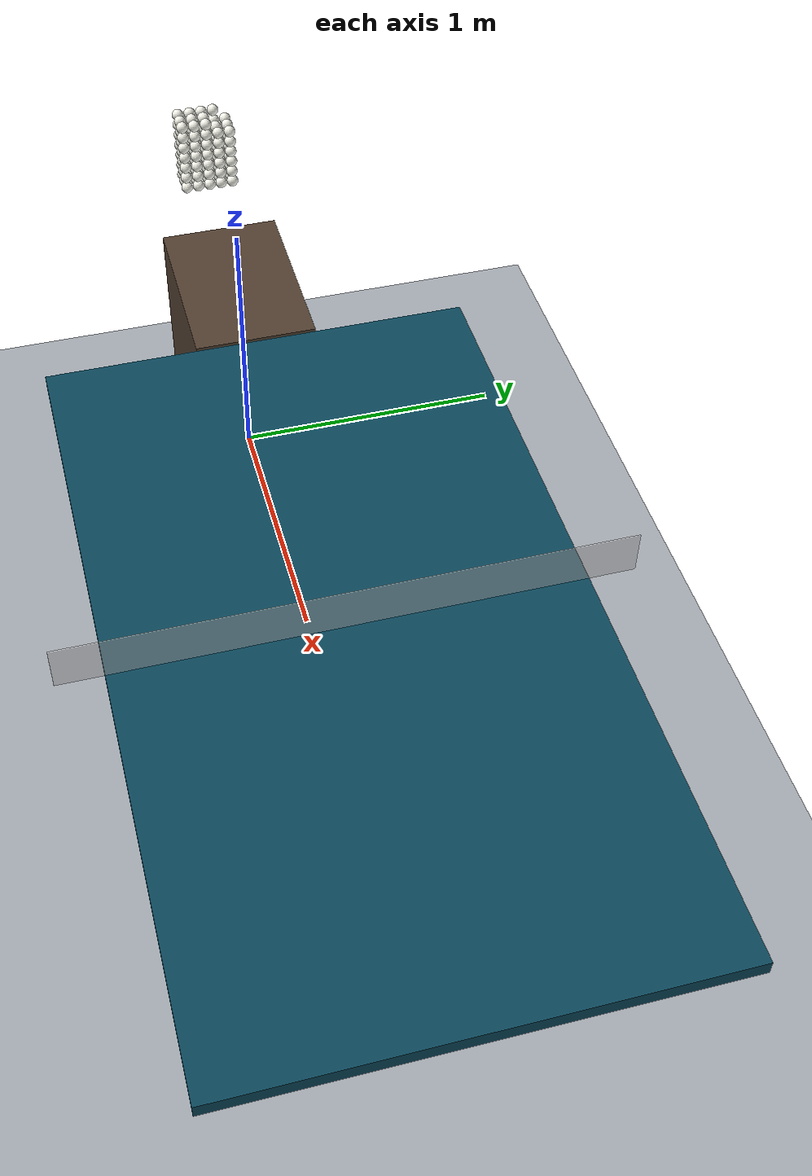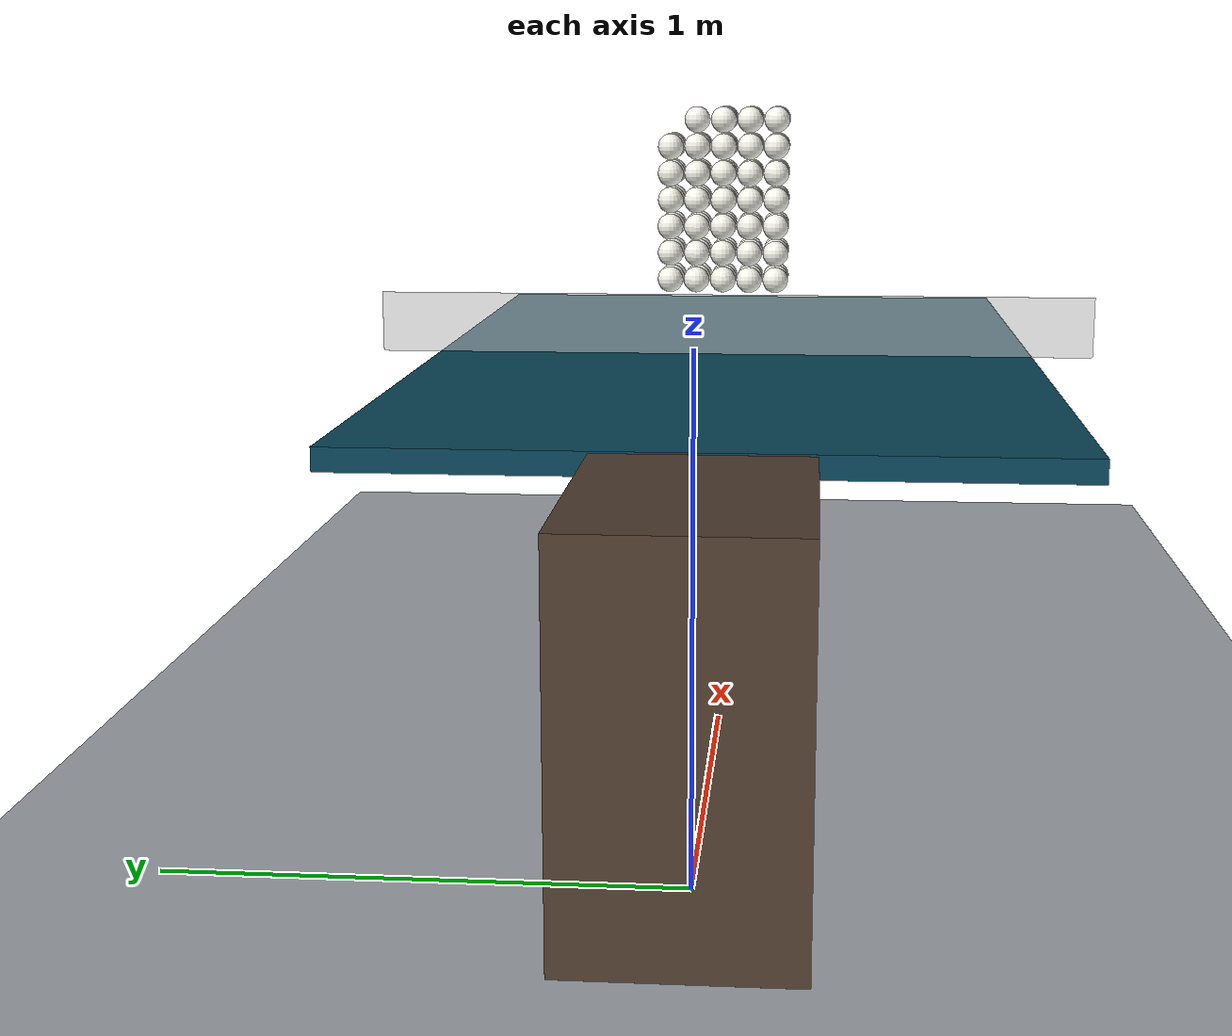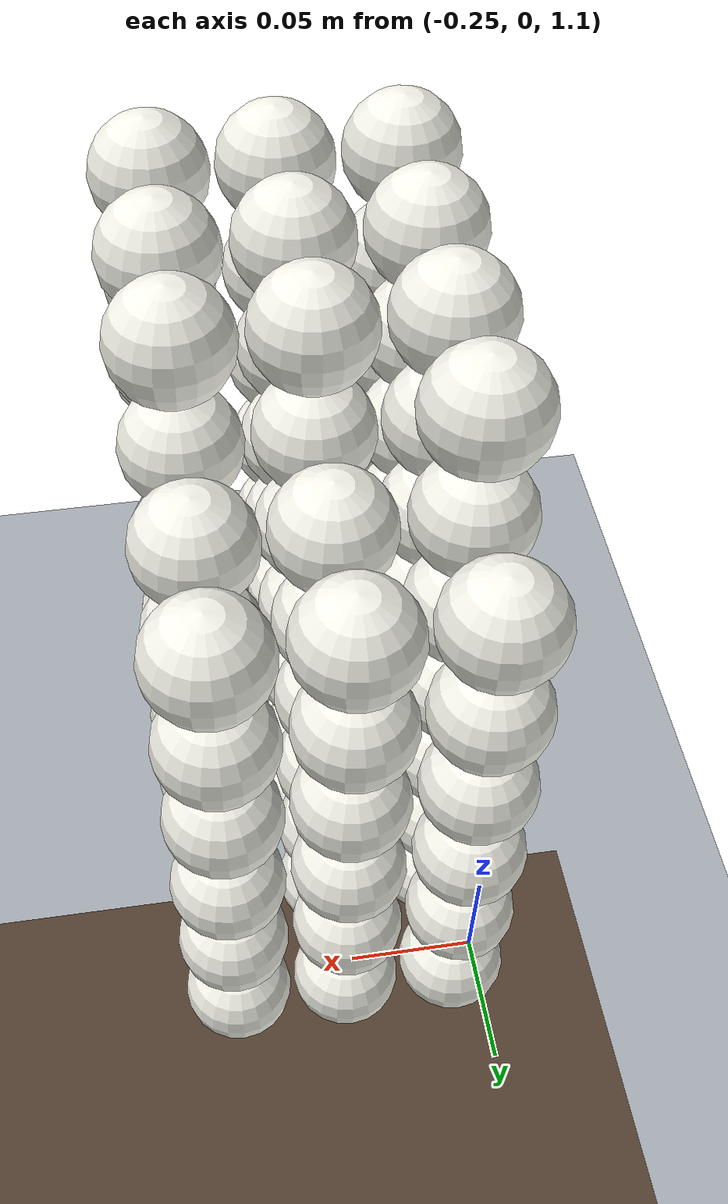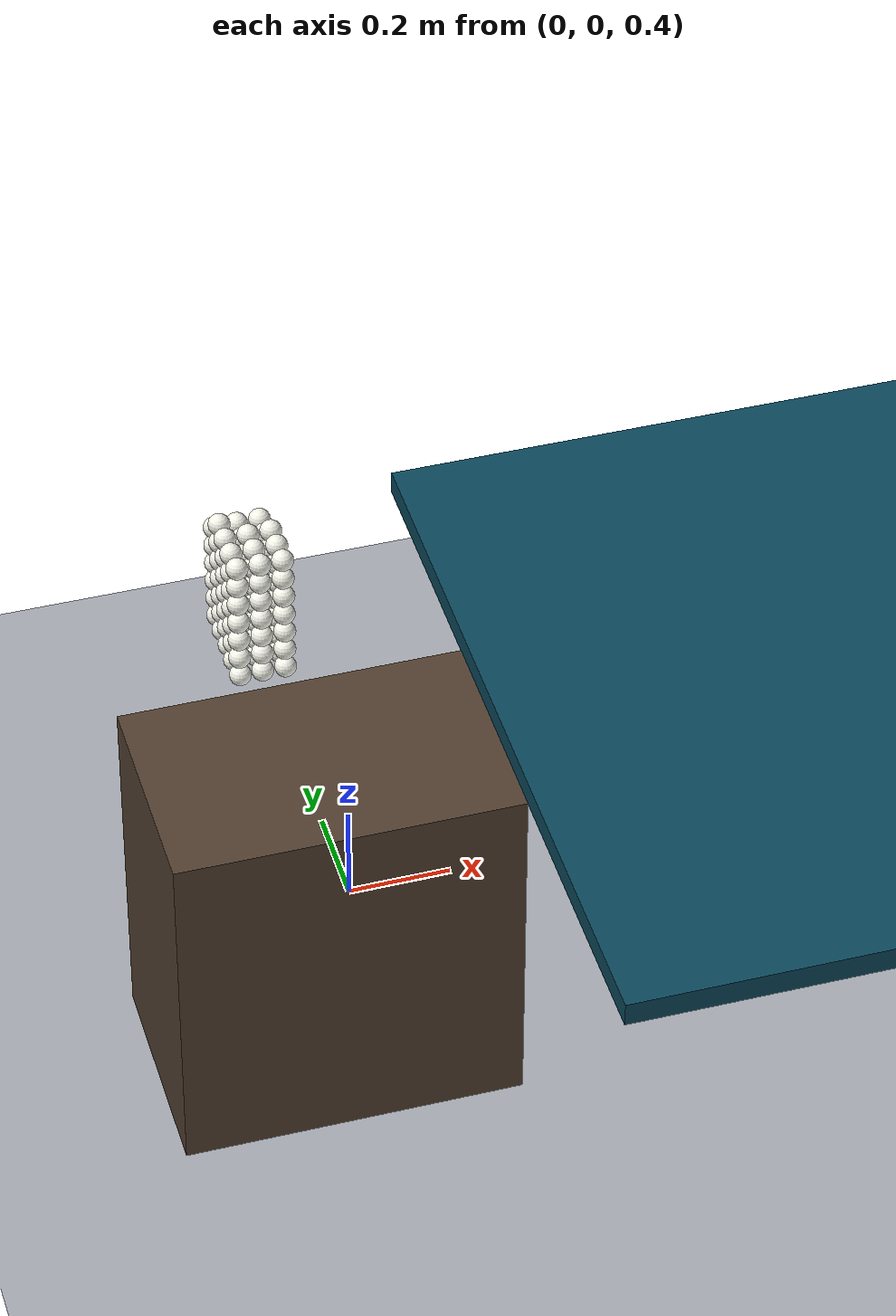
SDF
<sdf version="1.8">
 <world name="full_100_dart">
  <physics name="1ms" type="ignored">
   <max_step_size>0.001</max_step_size>
   <real_time_factor>1</real_time_factor>
   <dart><collision_detector>dart</collision_detector></dart>
  </physics>
  <gravity>0 0 -9.81</gravity>
  <plugin filename="ignition-gazebo-physics-system" name="ignition::gazebo::systems::Physics"/>
  <plugin filename="ignition-gazebo-user-commands-system" name="ignition::gazebo::systems::UserCommands"/>
  <plugin filename="ignition-gazebo-scene-broadcaster-system" name="ignition::gazebo::systems::SceneBroadcaster"/>
  <scene>
   <ambient>0.6 0.6 0.6 1</ambient>
   <background>0.85 0.89 0.94 1</background>
   <shadows>true</shadows>
  </scene>
  <light name="sun" type="directional">
   <pose>0 0 6 0 0 0</pose>
   <direction>-0.4 0.3 -1</direction>
   <diffuse>0.9 0.9 0.9 1</diffuse>
   <specular>0.2 0.2 0.2 1</specular>
  </light>
  <model name="ground">
   <static>true</static>
   <link name="ground_link">
    <collision name="floor">
     <geometry><plane><normal>0 0 1</normal><size>20 20</size></plane></geometry>
    </collision>
    <visual name="floor_visual">
     <geometry><plane><normal>0 0 1</normal><size>20 20</size></plane></geometry>
     <material><ambient>0.65 0.67 0.7 1</ambient><diffuse>0.65 0.67 0.7 1</diffuse></material>
    </visual>
   </link>
  </model>
  <model name="table">
   <static>true</static>
   <pose>1.6700000000000002 0.0 0.735 0.0 0.0 0.0</pose>
   <link name="top">
    <collision name="top">
     <geometry><box><size>2.74 1.525 0.05</size></box></geometry>
     <surface>
      <bounce><restitution_coefficient>0.85</restitution_coefficient><threshold>0.1</threshold></bounce>
      <friction><ode><mu>0.3</mu><mu2>0.3</mu2></ode></friction>
     </surface>
    </collision>
    <visual name="top_visual">
     <geometry><box><size>2.74 1.525 0.05</size></box></geometry>
     <material><ambient>0.04 0.28 0.36 1</ambient><diffuse>0.04 0.28 0.36 1</diffuse></material>
    </visual>
   </link>
  </model>
  <model name="net">
   <static>true</static>
   <pose>1.6700000000000002 0.0 0.83625 0.0 0.0 0.0</pose>
   <link name="net_link">
    <collision name="net"><geometry><box><size>0.005 1.83 0.1525</size></box></geometry></collision>
    <visual name="net_visual">
     <geometry><box><size>0.005 1.83 0.1525</size></box></geometry>
     <material><ambient>0.8 0.8 0.8 1</ambient><diffuse>0.8 0.8 0.8 1</diffuse></material>
     <transparency>0.45</transparency>
    </visual>
   </link>
  </model>
  <model name="launcher_bench">
   <static>true</static>
   <link name="bench">
    <collision name="bench">
     <pose>-0.0525 0 0.3795 0 0 0</pose>
     <geometry><box><size>0.675 0.44 0.759</size></box></geometry>
     <surface>
      <friction><ode><mu>0.3</mu><mu2>0.3</mu2></ode></friction>
      <bounce><restitution_coefficient>0.1</restitution_coefficient><threshold>0.1</threshold></bounce>
     </surface>
    </collision>
    <visual name="bench_visual">
     <pose>-0.0525 0 0.3795 0 0 0</pose>
     <geometry><box><size>0.675 0.44 0.759</size></box></geometry>
     <material><ambient>.32 .25 .19 1</ambient><diffuse>.32 .25 .19 1</diffuse></material>
    </visual>
   </link>
  </model>
  <model name="inventory_ball_001">
   <static>false</static>
   <pose>-0.23351634392092527 -0.14228499354686641 1.1430650175910217 0 0 0</pose>
   <link name="ball_link">
    <inertial>
     <mass>0.0027000000000000001</mass>
     <inertia>
      <ixx>7.1999999999999999e-07</ixx>
      <iyy>7.1999999999999999e-07</iyy>
      <izz>7.1999999999999999e-07</izz>
      <ixy>0</ixy>
      <ixz>0</ixz>
      <iyz>0</iyz>
     </inertia>
    </inertial>
    <collision name="ball_collision">
     <geometry><sphere><radius>0.02</radius></sphere></geometry>
     <surface>
      <friction><ode><mu>0.3</mu><mu2>0.3</mu2></ode></friction>
      <bounce><restitution_coefficient>0.8</restitution_coefficient><threshold>0.01</threshold></bounce>
     </surface>
    </collision>
    <visual name="ball_visual">
     <geometry><sphere><radius>0.02</radius></sphere></geometry>
     <material><ambient>0.96 0.96 0.92 1</ambient><diffuse>0.96 0.96 0.92 1</diffuse></material>
    </visual>
   </link>
  </model>
  <model name="inventory_ball_002">
   <static>false</static>
   <pose>-0.19216607355711071 -0.1418581172715016 1.143306019692454 0 0 0</pose>
   <link name="ball_link">
    <inertial>
     <mass>0.0027000000000000001</mass>
     <inertia>
      <ixx>7.1999999999999999e-07</ixx>
      <iyy>7.1999999999999999e-07</iyy>
      <izz>7.1999999999999999e-07</izz>
      <ixy>0</ixy>
      <ixz>0</ixz>
      <iyz>0</iyz>
     </inertia>
    </inertial>
    <collision name="ball_collision">
     <geometry><sphere><radius>0.02</radius></sphere></geometry>
     <surface>
      <friction><ode><mu>0.3</mu><mu2>0.3</mu2></ode></friction>
      <bounce><restitution_coefficient>0.8</restitution_coefficient><threshold>0.01</threshold></bounce>
     </surface>
    </collision>
    <visual name="ball_visual">
     <geometry><sphere><radius>0.02</radius></sphere></geometry>
     <material><ambient>0.96 0.96 0.92 1</ambient><diffuse>0.96 0.96 0.92 1</diffuse></material>
    </visual>
   </link>
  </model>
  <model name="inventory_ball_003">
   <static>false</static>
   <pose>-0.15016469225937706 -0.14224783670042238 1.1431531530918113 0 0 0</pose>
   <link name="ball_link">
    <inertial>
     <mass>0.0027000000000000001</mass>
     <inertia>
      <ixx>7.1999999999999999e-07</ixx>
      <iyy>7.1999999999999999e-07</iyy>
      <izz>7.1999999999999999e-07</izz>
      <ixy>0</ixy>
      <ixz>0</ixz>
      <iyz>0</iyz>
     </inertia>
    </inertial>
    <collision name="ball_collision">
     <geometry><sphere><radius>0.02</radius></sphere></geometry>
     <surface>
      <friction><ode><mu>0.3</mu><mu2>0.3</mu2></ode></friction>
      <bounce><restitution_coefficient>0.8</restitution_coefficient><threshold>0.01</threshold></bounce>
     </surface>
    </collision>
    <visual name="ball_visual">
     <geometry><sphere><radius>0.02</radius></sphere></geometry>
     <material><ambient>0.96 0.96 0.92 1</ambient><diffuse>0.96 0.96 0.92 1</diffuse></material>
    </visual>
   </link>
  </model>
  <model name="inventory_ball_004">
   <static>false</static>
   <pose>-0.23388212166833716 -0.10056881721511786 1.1432032131728622 0 0 0</pose>
   <link name="ball_link">
    <inertial>
     <mass>0.0027000000000000001</mass>
     <inertia>
      <ixx>7.1999999999999999e-07</ixx>
      <iyy>7.1999999999999999e-07</iyy>
      <izz>7.1999999999999999e-07</izz>
      <ixy>0</ixy>
      <ixz>0</ixz>
      <iyz>0</iyz>
     </inertia>
    </inertial>
    <collision name="ball_collision">
     <geometry><sphere><radius>0.02</radius></sphere></geometry>
     <surface>
      <friction><ode><mu>0.3</mu><mu2>0.3</mu2></ode></friction>
      <bounce><restitution_coefficient>0.8</restitution_coefficient><threshold>0.01</threshold></bounce>
     </surface>
    </collision>
    <visual name="ball_visual">
     <geometry><sphere><radius>0.02</radius></sphere></geometry>
     <material><ambient>0.96 0.96 0.92 1</ambient><diffuse>0.96 0.96 0.92 1</diffuse></material>
    </visual>
   </link>
  </model>
  <model name="inventory_ball_005">
   <static>false</static>
   <pose>-0.19228407841818967 -0.10058069740958803 1.1432899306626678 0 0 0</pose>
   <link name="ball_link">
    <inertial>
     <mass>0.0027000000000000001</mass>
     <inertia>
      <ixx>7.1999999999999999e-07</ixx>
      <iyy>7.1999999999999999e-07</iyy>
      <izz>7.1999999999999999e-07</izz>
      <ixy>0</ixy>
      <ixz>0</ixz>
      <iyz>0</iyz>
     </inertia>
    </inertial>
    <collision name="ball_collision">
     <geometry><sphere><radius>0.02</radius></sphere></geometry>
     <surface>
      <friction><ode><mu>0.3</mu><mu2>0.3</mu2></ode></friction>
      <bounce><restitution_coefficient>0.8</restitution_coefficient><threshold>0.01</threshold></bounce>
     </surface>
    </collision>
    <visual name="ball_visual">
     <geometry><sphere><radius>0.02</radius></sphere></geometry>
     <material><ambient>0.96 0.96 0.92 1</ambient><diffuse>0.96 0.96 0.92 1</diffuse></material>
    </visual>
   </link>
  </model>
  <model name="inventory_ball_006">
   <static>false</static>
   <pose>-0.15037303511163805 -0.1005677356267756 1.1432535594103257 0 0 0</pose>
   <link name="ball_link">
    <inertial>
     <mass>0.0027000000000000001</mass>
     <inertia>
      <ixx>7.1999999999999999e-07</ixx>
      <iyy>7.1999999999999999e-07</iyy>
      <izz>7.1999999999999999e-07</izz>
      <ixy>0</ixy>
      <ixz>0</ixz>
      <iyz>0</iyz>
     </inertia>
    </inertial>
    <collision name="ball_collision">
     <geometry><sphere><radius>0.02</radius></sphere></geometry>
     <surface>
      <friction><ode><mu>0.3</mu><mu2>0.3</mu2></ode></friction>
      <bounce><restitution_coefficient>0.8</restitution_coefficient><threshold>0.01</threshold></bounce>
     </surface>
    </collision>
    <visual name="ball_visual">
     <geometry><sphere><radius>0.02</radius></sphere></geometry>
     <material><ambient>0.96 0.96 0.92 1</ambient><diffuse>0.96 0.96 0.92 1</diffuse></material>
    </visual>
   </link>
  </model>
  <model name="inventory_ball_007">
   <static>false</static>
   <pose>-0.23341434172599332 -0.059096100744193171 1.1433834915510999 0 0 0</pose>
   <link name="ball_link">
    <inertial>
     <mass>0.0027000000000000001</mass>
     <inertia>
      <ixx>7.1999999999999999e-07</ixx>
      <iyy>7.1999999999999999e-07</iyy>
      <izz>7.1999999999999999e-07</izz>
      <ixy>0</ixy>
      <ixz>0</ixz>
      <iyz>0</iyz>
     </inertia>
    </inertial>
    <collision name="ball_collision">
     <geometry><sphere><radius>0.02</radius></sphere></geometry>
     <surface>
      <friction><ode><mu>0.3</mu><mu2>0.3</mu2></ode></friction>
      <bounce><restitution_coefficient>0.8</restitution_coefficient><threshold>0.01</threshold></bounce>
     </surface>
    </collision>
    <visual name="ball_visual">
     <geometry><sphere><radius>0.02</radius></sphere></geometry>
     <material><ambient>0.96 0.96 0.92 1</ambient><diffuse>0.96 0.96 0.92 1</diffuse></material>
    </visual>
   </link>
  </model>
  <model name="inventory_ball_008">
   <static>false</static>
   <pose>-0.19188111636300706 -0.058895849690089208 1.1429932876998874 0 0 0</pose>
   <link name="ball_link">
    <inertial>
     <mass>0.0027000000000000001</mass>
     <inertia>
      <ixx>7.1999999999999999e-07</ixx>
      <iyy>7.1999999999999999e-07</iyy>
      <izz>7.1999999999999999e-07</izz>
      <ixy>0</ixy>
      <ixz>0</ixz>
      <iyz>0</iyz>
     </inertia>
    </inertial>
    <collision name="ball_collision">
     <geometry><sphere><radius>0.02</radius></sphere></geometry>
     <surface>
      <friction><ode><mu>0.3</mu><mu2>0.3</mu2></ode></friction>
      <bounce><restitution_coefficient>0.8</restitution_coefficient><threshold>0.01</threshold></bounce>
     </surface>
    </collision>
    <visual name="ball_visual">
     <geometry><sphere><radius>0.02</radius></sphere></geometry>
     <material><ambient>0.96 0.96 0.92 1</ambient><diffuse>0.96 0.96 0.92 1</diffuse></material>
    </visual>
   </link>
  </model>
  <model name="inventory_ball_009">
   <static>false</static>
   <pose>-0.15012567215667591 -0.058898043272932431 1.1429556475060283 0 0 0</pose>
   <link name="ball_link">
    <inertial>
     <mass>0.0027000000000000001</mass>
     <inertia>
      <ixx>7.1999999999999999e-07</ixx>
      <iyy>7.1999999999999999e-07</iyy>
      <izz>7.1999999999999999e-07</izz>
      <ixy>0</ixy>
      <ixz>0</ixz>
      <iyz>0</iyz>
     </inertia>
    </inertial>
    <collision name="ball_collision">
     <geometry><sphere><radius>0.02</radius></sphere></geometry>
     <surface>
      <friction><ode><mu>0.3</mu><mu2>0.3</mu2></ode></friction>
      <bounce><restitution_coefficient>0.8</restitution_coefficient><threshold>0.01</threshold></bounce>
     </surface>
    </collision>
    <visual name="ball_visual">
     <geometry><sphere><radius>0.02</radius></sphere></geometry>
     <material><ambient>0.96 0.96 0.92 1</ambient><diffuse>0.96 0.96 0.92 1</diffuse></material>
    </visual>
   </link>
  </model>
  <model name="inventory_ball_010">
   <static>false</static>
   <pose>-0.23384197017389993 -0.016991503380191519 1.1432622356188205 0 0 0</pose>
   <link name="ball_link">
    <inertial>
     <mass>0.0027000000000000001</mass>
     <inertia>
      <ixx>7.1999999999999999e-07</ixx>
      <iyy>7.1999999999999999e-07</iyy>
      <izz>7.1999999999999999e-07</izz>
      <ixy>0</ixy>
      <ixz>0</ixz>
      <iyz>0</iyz>
     </inertia>
    </inertial>
    <collision name="ball_collision">
     <geometry><sphere><radius>0.02</radius></sphere></geometry>
     <surface>
      <friction><ode><mu>0.3</mu><mu2>0.3</mu2></ode></friction>
      <bounce><restitution_coefficient>0.8</restitution_coefficient><threshold>0.01</threshold></bounce>
     </surface>
    </collision>
    <visual name="ball_visual">
     <geometry><sphere><radius>0.02</radius></sphere></geometry>
     <material><ambient>0.96 0.96 0.92 1</ambient><diffuse>0.96 0.96 0.92 1</diffuse></material>
    </visual>
   </link>
  </model>
  <model name="inventory_ball_011">
   <static>false</static>
   <pose>-0.19181572303603536 -0.017062160927983704 1.1432217368548729 0 0 0</pose>
   <link name="ball_link">
    <inertial>
     <mass>0.0027000000000000001</mass>
     <inertia>
      <ixx>7.1999999999999999e-07</ixx>
      <iyy>7.1999999999999999e-07</iyy>
      <izz>7.1999999999999999e-07</izz>
      <ixy>0</ixy>
      <ixz>0</ixz>
      <iyz>0</iyz>
     </inertia>
    </inertial>
    <collision name="ball_collision">
     <geometry><sphere><radius>0.02</radius></sphere></geometry>
     <surface>
      <friction><ode><mu>0.3</mu><mu2>0.3</mu2></ode></friction>
      <bounce><restitution_coefficient>0.8</restitution_coefficient><threshold>0.01</threshold></bounce>
     </surface>
    </collision>
    <visual name="ball_visual">
     <geometry><sphere><radius>0.02</radius></sphere></geometry>
     <material><ambient>0.96 0.96 0.92 1</ambient><diffuse>0.96 0.96 0.92 1</diffuse></material>
    </visual>
   </link>
  </model>
  <model name="inventory_ball_012">
   <static>false</static>
   <pose>-0.15011613054161235 -0.017272879373674981 1.1432312243787641 0 0 0</pose>
   <link name="ball_link">
    <inertial>
     <mass>0.0027000000000000001</mass>
     <inertia>
      <ixx>7.1999999999999999e-07</ixx>
      <iyy>7.1999999999999999e-07</iyy>
      <izz>7.1999999999999999e-07</izz>
      <ixy>0</ixy>
      <ixz>0</ixz>
      <iyz>0</iyz>
     </inertia>
    </inertial>
    <collision name="ball_collision">
     <geometry><sphere><radius>0.02</radius></sphere></geometry>
     <surface>
      <friction><ode><mu>0.3</mu><mu2>0.3</mu2></ode></friction>
      <bounce><restitution_coefficient>0.8</restitution_coefficient><threshold>0.01</threshold></bounce>
     </surface>
    </collision>
    <visual name="ball_visual">
     <geometry><sphere><radius>0.02</radius></sphere></geometry>
     <material><ambient>0.96 0.96 0.92 1</ambient><diffuse>0.96 0.96 0.92 1</diffuse></material>
    </visual>
   </link>
  </model>
  <model name="inventory_ball_013">
   <static>false</static>
   <pose>-0.2334023572014482 0.024471111851418554 1.1434170241401866 0 0 0</pose>
   <link name="ball_link">
    <inertial>
     <mass>0.0027000000000000001</mass>
     <inertia>
      <ixx>7.1999999999999999e-07</ixx>
      <iyy>7.1999999999999999e-07</iyy>
      <izz>7.1999999999999999e-07</izz>
      <ixy>0</ixy>
      <ixz>0</ixz>
      <iyz>0</iyz>
     </inertia>
    </inertial>
    <collision name="ball_collision">
     <geometry><sphere><radius>0.02</radius></sphere></geometry>
     <surface>
      <friction><ode><mu>0.3</mu><mu2>0.3</mu2></ode></friction>
      <bounce><restitution_coefficient>0.8</restitution_coefficient><threshold>0.01</threshold></bounce>
     </surface>
    </collision>
    <visual name="ball_visual">
     <geometry><sphere><radius>0.02</radius></sphere></geometry>
     <material><ambient>0.96 0.96 0.92 1</ambient><diffuse>0.96 0.96 0.92 1</diffuse></material>
    </visual>
   </link>
  </model>
  <model name="inventory_ball_014">
   <static>false</static>
   <pose>-0.19195358871284596 0.024522743101728958 1.1429274946301937 0 0 0</pose>
   <link name="ball_link">
    <inertial>
     <mass>0.0027000000000000001</mass>
     <inertia>
      <ixx>7.1999999999999999e-07</ixx>
      <iyy>7.1999999999999999e-07</iyy>
      <izz>7.1999999999999999e-07</izz>
      <ixy>0</ixy>
      <ixz>0</ixz>
      <iyz>0</iyz>
     </inertia>
    </inertial>
    <collision name="ball_collision">
     <geometry><sphere><radius>0.02</radius></sphere></geometry>
     <surface>
      <friction><ode><mu>0.3</mu><mu2>0.3</mu2></ode></friction>
      <bounce><restitution_coefficient>0.8</restitution_coefficient><threshold>0.01</threshold></bounce>
     </surface>
    </collision>
    <visual name="ball_visual">
     <geometry><sphere><radius>0.02</radius></sphere></geometry>
     <material><ambient>0.96 0.96 0.92 1</ambient><diffuse>0.96 0.96 0.92 1</diffuse></material>
    </visual>
   </link>
  </model>
  <model name="inventory_ball_015">
   <static>false</static>
   <pose>-0.15056326103460904 0.024273632778161268 1.1429478751861544 0 0 0</pose>
   <link name="ball_link">
    <inertial>
     <mass>0.0027000000000000001</mass>
     <inertia>
      <ixx>7.1999999999999999e-07</ixx>
      <iyy>7.1999999999999999e-07</iyy>
      <izz>7.1999999999999999e-07</izz>
      <ixy>0</ixy>
      <ixz>0</ixz>
      <iyz>0</iyz>
     </inertia>
    </inertial>
    <collision name="ball_collision">
     <geometry><sphere><radius>0.02</radius></sphere></geometry>
     <surface>
      <friction><ode><mu>0.3</mu><mu2>0.3</mu2></ode></friction>
      <bounce><restitution_coefficient>0.8</restitution_coefficient><threshold>0.01</threshold></bounce>
     </surface>
    </collision>
    <visual name="ball_visual">
     <geometry><sphere><radius>0.02</radius></sphere></geometry>
     <material><ambient>0.96 0.96 0.92 1</ambient><diffuse>0.96 0.96 0.92 1</diffuse></material>
    </visual>
   </link>
  </model>
  <model name="inventory_ball_016">
   <static>false</static>
   <pose>-0.23376032546818337 -0.14223939914235417 1.1846667841618663 0 0 0</pose>
   <link name="ball_link">
    <inertial>
     <mass>0.0027000000000000001</mass>
     <inertia>
      <ixx>7.1999999999999999e-07</ixx>
      <iyy>7.1999999999999999e-07</iyy>
      <izz>7.1999999999999999e-07</izz>
      <ixy>0</ixy>
      <ixz>0</ixz>
      <iyz>0</iyz>
     </inertia>
    </inertial>
    <collision name="ball_collision">
     <geometry><sphere><radius>0.02</radius></sphere></geometry>
     <surface>
      <friction><ode><mu>0.3</mu><mu2>0.3</mu2></ode></friction>
      <bounce><restitution_coefficient>0.8</restitution_coefficient><threshold>0.01</threshold></bounce>
     </surface>
    </collision>
    <visual name="ball_visual">
     <geometry><sphere><radius>0.02</radius></sphere></geometry>
     <material><ambient>0.96 0.96 0.92 1</ambient><diffuse>0.96 0.96 0.92 1</diffuse></material>
    </visual>
   </link>
  </model>
  <model name="inventory_ball_017">
   <static>false</static>
   <pose>-0.19191858933344136 -0.14208110069261795 1.1847221085802704 0 0 0</pose>
   <link name="ball_link">
    <inertial>
     <mass>0.0027000000000000001</mass>
     <inertia>
      <ixx>7.1999999999999999e-07</ixx>
      <iyy>7.1999999999999999e-07</iyy>
      <izz>7.1999999999999999e-07</izz>
      <ixy>0</ixy>
      <ixz>0</ixz>
      <iyz>0</iyz>
     </inertia>
    </inertial>
    <collision name="ball_collision">
     <geometry><sphere><radius>0.02</radius></sphere></geometry>
     <surface>
      <friction><ode><mu>0.3</mu><mu2>0.3</mu2></ode></friction>
      <bounce><restitution_coefficient>0.8</restitution_coefficient><threshold>0.01</threshold></bounce>
     </surface>
    </collision>
    <visual name="ball_visual">
     <geometry><sphere><radius>0.02</radius></sphere></geometry>
     <material><ambient>0.96 0.96 0.92 1</ambient><diffuse>0.96 0.96 0.92 1</diffuse></material>
    </visual>
   </link>
  </model>
  <model name="inventory_ball_018">
   <static>false</static>
   <pose>-0.15057429578153708 -0.14213981330677056 1.1850619927526278 0 0 0</pose>
   <link name="ball_link">
    <inertial>
     <mass>0.0027000000000000001</mass>
     <inertia>
      <ixx>7.1999999999999999e-07</ixx>
      <iyy>7.1999999999999999e-07</iyy>
      <izz>7.1999999999999999e-07</izz>
      <ixy>0</ixy>
      <ixz>0</ixz>
      <iyz>0</iyz>
     </inertia>
    </inertial>
    <collision name="ball_collision">
     <geometry><sphere><radius>0.02</radius></sphere></geometry>
     <surface>
      <friction><ode><mu>0.3</mu><mu2>0.3</mu2></ode></friction>
      <bounce><restitution_coefficient>0.8</restitution_coefficient><threshold>0.01</threshold></bounce>
     </surface>
    </collision>
    <visual name="ball_visual">
     <geometry><sphere><radius>0.02</radius></sphere></geometry>
     <material><ambient>0.96 0.96 0.92 1</ambient><diffuse>0.96 0.96 0.92 1</diffuse></material>
    </visual>
   </link>
  </model>
  <model name="inventory_ball_019">
   <static>false</static>
   <pose>-0.23351117876885205 -0.10033452139659982 1.1846026831889191 0 0 0</pose>
   <link name="ball_link">
    <inertial>
     <mass>0.0027000000000000001</mass>
     <inertia>
      <ixx>7.1999999999999999e-07</ixx>
      <iyy>7.1999999999999999e-07</iyy>
      <izz>7.1999999999999999e-07</izz>
      <ixy>0</ixy>
      <ixz>0</ixz>
      <iyz>0</iyz>
     </inertia>
    </inertial>
    <collision name="ball_collision">
     <geometry><sphere><radius>0.02</radius></sphere></geometry>
     <surface>
      <friction><ode><mu>0.3</mu><mu2>0.3</mu2></ode></friction>
      <bounce><restitution_coefficient>0.8</restitution_coefficient><threshold>0.01</threshold></bounce>
     </surface>
    </collision>
    <visual name="ball_visual">
     <geometry><sphere><radius>0.02</radius></sphere></geometry>
     <material><ambient>0.96 0.96 0.92 1</ambient><diffuse>0.96 0.96 0.92 1</diffuse></material>
    </visual>
   </link>
  </model>
  <model name="inventory_ball_020">
   <static>false</static>
   <pose>-0.19186252392122979 -0.10060195850374286 1.1847276732650549 0 0 0</pose>
   <link name="ball_link">
    <inertial>
     <mass>0.0027000000000000001</mass>
     <inertia>
      <ixx>7.1999999999999999e-07</ixx>
      <iyy>7.1999999999999999e-07</iyy>
      <izz>7.1999999999999999e-07</izz>
      <ixy>0</ixy>
      <ixz>0</ixz>
      <iyz>0</iyz>
     </inertia>
    </inertial>
    <collision name="ball_collision">
     <geometry><sphere><radius>0.02</radius></sphere></geometry>
     <surface>
      <friction><ode><mu>0.3</mu><mu2>0.3</mu2></ode></friction>
      <bounce><restitution_coefficient>0.8</restitution_coefficient><threshold>0.01</threshold></bounce>
     </surface>
    </collision>
    <visual name="ball_visual">
     <geometry><sphere><radius>0.02</radius></sphere></geometry>
     <material><ambient>0.96 0.96 0.92 1</ambient><diffuse>0.96 0.96 0.92 1</diffuse></material>
    </visual>
   </link>
  </model>
  <model name="inventory_ball_021">
   <static>false</static>
   <pose>-0.15010628598961803 -0.10031600014408756 1.184834169846265 0 0 0</pose>
   <link name="ball_link">
    <inertial>
     <mass>0.0027000000000000001</mass>
     <inertia>
      <ixx>7.1999999999999999e-07</ixx>
      <iyy>7.1999999999999999e-07</iyy>
      <izz>7.1999999999999999e-07</izz>
      <ixy>0</ixy>
      <ixz>0</ixz>
      <iyz>0</iyz>
     </inertia>
    </inertial>
    <collision name="ball_collision">
     <geometry><sphere><radius>0.02</radius></sphere></geometry>
     <surface>
      <friction><ode><mu>0.3</mu><mu2>0.3</mu2></ode></friction>
      <bounce><restitution_coefficient>0.8</restitution_coefficient><threshold>0.01</threshold></bounce>
     </surface>
    </collision>
    <visual name="ball_visual">
     <geometry><sphere><radius>0.02</radius></sphere></geometry>
     <material><ambient>0.96 0.96 0.92 1</ambient><diffuse>0.96 0.96 0.92 1</diffuse></material>
    </visual>
   </link>
  </model>
  <model name="inventory_ball_022">
   <static>false</static>
   <pose>-0.23348923144940609 -0.058594288847886117 1.184965599946928 0 0 0</pose>
   <link name="ball_link">
    <inertial>
     <mass>0.0027000000000000001</mass>
     <inertia>
      <ixx>7.1999999999999999e-07</ixx>
      <iyy>7.1999999999999999e-07</iyy>
      <izz>7.1999999999999999e-07</izz>
      <ixy>0</ixy>
      <ixz>0</ixz>
      <iyz>0</iyz>
     </inertia>
    </inertial>
    <collision name="ball_collision">
     <geometry><sphere><radius>0.02</radius></sphere></geometry>
     <surface>
      <friction><ode><mu>0.3</mu><mu2>0.3</mu2></ode></friction>
      <bounce><restitution_coefficient>0.8</restitution_coefficient><threshold>0.01</threshold></bounce>
     </surface>
    </collision>
    <visual name="ball_visual">
     <geometry><sphere><radius>0.02</radius></sphere></geometry>
     <material><ambient>0.96 0.96 0.92 1</ambient><diffuse>0.96 0.96 0.92 1</diffuse></material>
    </visual>
   </link>
  </model>
  <model name="inventory_ball_023">
   <static>false</static>
   <pose>-0.19216257115682153 -0.059080739853657582 1.1846892718288358 0 0 0</pose>
   <link name="ball_link">
    <inertial>
     <mass>0.0027000000000000001</mass>
     <inertia>
      <ixx>7.1999999999999999e-07</ixx>
      <iyy>7.1999999999999999e-07</iyy>
      <izz>7.1999999999999999e-07</izz>
      <ixy>0</ixy>
      <ixz>0</ixz>
      <iyz>0</iyz>
     </inertia>
    </inertial>
    <collision name="ball_collision">
     <geometry><sphere><radius>0.02</radius></sphere></geometry>
     <surface>
      <friction><ode><mu>0.3</mu><mu2>0.3</mu2></ode></friction>
      <bounce><restitution_coefficient>0.8</restitution_coefficient><threshold>0.01</threshold></bounce>
     </surface>
    </collision>
    <visual name="ball_visual">
     <geometry><sphere><radius>0.02</radius></sphere></geometry>
     <material><ambient>0.96 0.96 0.92 1</ambient><diffuse>0.96 0.96 0.92 1</diffuse></material>
    </visual>
   </link>
  </model>
  <model name="inventory_ball_024">
   <static>false</static>
   <pose>-0.15053935547441455 -0.058973410293848207 1.1850657458286014 0 0 0</pose>
   <link name="ball_link">
    <inertial>
     <mass>0.0027000000000000001</mass>
     <inertia>
      <ixx>7.1999999999999999e-07</ixx>
      <iyy>7.1999999999999999e-07</iyy>
      <izz>7.1999999999999999e-07</izz>
      <ixy>0</ixy>
      <ixz>0</ixz>
      <iyz>0</iyz>
     </inertia>
    </inertial>
    <collision name="ball_collision">
     <geometry><sphere><radius>0.02</radius></sphere></geometry>
     <surface>
      <friction><ode><mu>0.3</mu><mu2>0.3</mu2></ode></friction>
      <bounce><restitution_coefficient>0.8</restitution_coefficient><threshold>0.01</threshold></bounce>
     </surface>
    </collision>
    <visual name="ball_visual">
     <geometry><sphere><radius>0.02</radius></sphere></geometry>
     <material><ambient>0.96 0.96 0.92 1</ambient><diffuse>0.96 0.96 0.92 1</diffuse></material>
    </visual>
   </link>
  </model>
  <model name="inventory_ball_025">
   <static>false</static>
   <pose>-0.2333741794241164 -0.017311193271520905 1.1848932631991773 0 0 0</pose>
   <link name="ball_link">
    <inertial>
     <mass>0.0027000000000000001</mass>
     <inertia>
      <ixx>7.1999999999999999e-07</ixx>
      <iyy>7.1999999999999999e-07</iyy>
      <izz>7.1999999999999999e-07</izz>
      <ixy>0</ixy>
      <ixz>0</ixz>
      <iyz>0</iyz>
     </inertia>
    </inertial>
    <collision name="ball_collision">
     <geometry><sphere><radius>0.02</radius></sphere></geometry>
     <surface>
      <friction><ode><mu>0.3</mu><mu2>0.3</mu2></ode></friction>
      <bounce><restitution_coefficient>0.8</restitution_coefficient><threshold>0.01</threshold></bounce>
     </surface>
    </collision>
    <visual name="ball_visual">
     <geometry><sphere><radius>0.02</radius></sphere></geometry>
     <material><ambient>0.96 0.96 0.92 1</ambient><diffuse>0.96 0.96 0.92 1</diffuse></material>
    </visual>
   </link>
  </model>
  <model name="inventory_ball_026">
   <static>false</static>
   <pose>-0.1920626208593636 -0.016951271446155668 1.1847753111115527 0 0 0</pose>
   <link name="ball_link">
    <inertial>
     <mass>0.0027000000000000001</mass>
     <inertia>
      <ixx>7.1999999999999999e-07</ixx>
      <iyy>7.1999999999999999e-07</iyy>
      <izz>7.1999999999999999e-07</izz>
      <ixy>0</ixy>
      <ixz>0</ixz>
      <iyz>0</iyz>
     </inertia>
    </inertial>
    <collision name="ball_collision">
     <geometry><sphere><radius>0.02</radius></sphere></geometry>
     <surface>
      <friction><ode><mu>0.3</mu><mu2>0.3</mu2></ode></friction>
      <bounce><restitution_coefficient>0.8</restitution_coefficient><threshold>0.01</threshold></bounce>
     </surface>
    </collision>
    <visual name="ball_visual">
     <geometry><sphere><radius>0.02</radius></sphere></geometry>
     <material><ambient>0.96 0.96 0.92 1</ambient><diffuse>0.96 0.96 0.92 1</diffuse></material>
    </visual>
   </link>
  </model>
  <model name="inventory_ball_027">
   <static>false</static>
   <pose>-0.15054107190010116 -0.017352023495383603 1.1848368208804982 0 0 0</pose>
   <link name="ball_link">
    <inertial>
     <mass>0.0027000000000000001</mass>
     <inertia>
      <ixx>7.1999999999999999e-07</ixx>
      <iyy>7.1999999999999999e-07</iyy>
      <izz>7.1999999999999999e-07</izz>
      <ixy>0</ixy>
      <ixz>0</ixz>
      <iyz>0</iyz>
     </inertia>
    </inertial>
    <collision name="ball_collision">
     <geometry><sphere><radius>0.02</radius></sphere></geometry>
     <surface>
      <friction><ode><mu>0.3</mu><mu2>0.3</mu2></ode></friction>
      <bounce><restitution_coefficient>0.8</restitution_coefficient><threshold>0.01</threshold></bounce>
     </surface>
    </collision>
    <visual name="ball_visual">
     <geometry><sphere><radius>0.02</radius></sphere></geometry>
     <material><ambient>0.96 0.96 0.92 1</ambient><diffuse>0.96 0.96 0.92 1</diffuse></material>
    </visual>
   </link>
  </model>
  <model name="inventory_ball_028">
   <static>false</static>
   <pose>-0.23374235503488625 0.024450751594134131 1.1850386937301618 0 0 0</pose>
   <link name="ball_link">
    <inertial>
     <mass>0.0027000000000000001</mass>
     <inertia>
      <ixx>7.1999999999999999e-07</ixx>
      <iyy>7.1999999999999999e-07</iyy>
      <izz>7.1999999999999999e-07</izz>
      <ixy>0</ixy>
      <ixz>0</ixz>
      <iyz>0</iyz>
     </inertia>
    </inertial>
    <collision name="ball_collision">
     <geometry><sphere><radius>0.02</radius></sphere></geometry>
     <surface>
      <friction><ode><mu>0.3</mu><mu2>0.3</mu2></ode></friction>
      <bounce><restitution_coefficient>0.8</restitution_coefficient><threshold>0.01</threshold></bounce>
     </surface>
    </collision>
    <visual name="ball_visual">
     <geometry><sphere><radius>0.02</radius></sphere></geometry>
     <material><ambient>0.96 0.96 0.92 1</ambient><diffuse>0.96 0.96 0.92 1</diffuse></material>
    </visual>
   </link>
  </model>
  <model name="inventory_ball_029">
   <static>false</static>
   <pose>-0.19206035969691576 0.024231592455494375 1.1850985225638975 0 0 0</pose>
   <link name="ball_link">
    <inertial>
     <mass>0.0027000000000000001</mass>
     <inertia>
      <ixx>7.1999999999999999e-07</ixx>
      <iyy>7.1999999999999999e-07</iyy>
      <izz>7.1999999999999999e-07</izz>
      <ixy>0</ixy>
      <ixz>0</ixz>
      <iyz>0</iyz>
     </inertia>
    </inertial>
    <collision name="ball_collision">
     <geometry><sphere><radius>0.02</radius></sphere></geometry>
     <surface>
      <friction><ode><mu>0.3</mu><mu2>0.3</mu2></ode></friction>
      <bounce><restitution_coefficient>0.8</restitution_coefficient><threshold>0.01</threshold></bounce>
     </surface>
    </collision>
    <visual name="ball_visual">
     <geometry><sphere><radius>0.02</radius></sphere></geometry>
     <material><ambient>0.96 0.96 0.92 1</ambient><diffuse>0.96 0.96 0.92 1</diffuse></material>
    </visual>
   </link>
  </model>
  <model name="inventory_ball_030">
   <static>false</static>
   <pose>-0.15039428422379411 0.024154545647304283 1.1845282698252551 0 0 0</pose>
   <link name="ball_link">
    <inertial>
     <mass>0.0027000000000000001</mass>
     <inertia>
      <ixx>7.1999999999999999e-07</ixx>
      <iyy>7.1999999999999999e-07</iyy>
      <izz>7.1999999999999999e-07</izz>
      <ixy>0</ixy>
      <ixz>0</ixz>
      <iyz>0</iyz>
     </inertia>
    </inertial>
    <collision name="ball_collision">
     <geometry><sphere><radius>0.02</radius></sphere></geometry>
     <surface>
      <friction><ode><mu>0.3</mu><mu2>0.3</mu2></ode></friction>
      <bounce><restitution_coefficient>0.8</restitution_coefficient><threshold>0.01</threshold></bounce>
     </surface>
    </collision>
    <visual name="ball_visual">
     <geometry><sphere><radius>0.02</radius></sphere></geometry>
     <material><ambient>0.96 0.96 0.92 1</ambient><diffuse>0.96 0.96 0.92 1</diffuse></material>
    </visual>
   </link>
  </model>
  <model name="inventory_ball_031">
   <static>false</static>
   <pose>-0.2338342105217896 -0.14192353237497815 1.226575247618618 0 0 0</pose>
   <link name="ball_link">
    <inertial>
     <mass>0.0027000000000000001</mass>
     <inertia>
      <ixx>7.1999999999999999e-07</ixx>
      <iyy>7.1999999999999999e-07</iyy>
      <izz>7.1999999999999999e-07</izz>
      <ixy>0</ixy>
      <ixz>0</ixz>
      <iyz>0</iyz>
     </inertia>
    </inertial>
    <collision name="ball_collision">
     <geometry><sphere><radius>0.02</radius></sphere></geometry>
     <surface>
      <friction><ode><mu>0.3</mu><mu2>0.3</mu2></ode></friction>
      <bounce><restitution_coefficient>0.8</restitution_coefficient><threshold>0.01</threshold></bounce>
     </surface>
    </collision>
    <visual name="ball_visual">
     <geometry><sphere><radius>0.02</radius></sphere></geometry>
     <material><ambient>0.96 0.96 0.92 1</ambient><diffuse>0.96 0.96 0.92 1</diffuse></material>
    </visual>
   </link>
  </model>
  <model name="inventory_ball_032">
   <static>false</static>
   <pose>-0.19204670401992019 -0.14226188337630885 1.2263289715719041 0 0 0</pose>
   <link name="ball_link">
    <inertial>
     <mass>0.0027000000000000001</mass>
     <inertia>
      <ixx>7.1999999999999999e-07</ixx>
      <iyy>7.1999999999999999e-07</iyy>
      <izz>7.1999999999999999e-07</izz>
      <ixy>0</ixy>
      <ixz>0</ixz>
      <iyz>0</iyz>
     </inertia>
    </inertial>
    <collision name="ball_collision">
     <geometry><sphere><radius>0.02</radius></sphere></geometry>
     <surface>
      <friction><ode><mu>0.3</mu><mu2>0.3</mu2></ode></friction>
      <bounce><restitution_coefficient>0.8</restitution_coefficient><threshold>0.01</threshold></bounce>
     </surface>
    </collision>
    <visual name="ball_visual">
     <geometry><sphere><radius>0.02</radius></sphere></geometry>
     <material><ambient>0.96 0.96 0.92 1</ambient><diffuse>0.96 0.96 0.92 1</diffuse></material>
    </visual>
   </link>
  </model>
  <model name="inventory_ball_033">
   <static>false</static>
   <pose>-0.15010232717185593 -0.14198253139294054 1.2266826470265684 0 0 0</pose>
   <link name="ball_link">
    <inertial>
     <mass>0.0027000000000000001</mass>
     <inertia>
      <ixx>7.1999999999999999e-07</ixx>
      <iyy>7.1999999999999999e-07</iyy>
      <izz>7.1999999999999999e-07</izz>
      <ixy>0</ixy>
      <ixz>0</ixz>
      <iyz>0</iyz>
     </inertia>
    </inertial>
    <collision name="ball_collision">
     <geometry><sphere><radius>0.02</radius></sphere></geometry>
     <surface>
      <friction><ode><mu>0.3</mu><mu2>0.3</mu2></ode></friction>
      <bounce><restitution_coefficient>0.8</restitution_coefficient><threshold>0.01</threshold></bounce>
     </surface>
    </collision>
    <visual name="ball_visual">
     <geometry><sphere><radius>0.02</radius></sphere></geometry>
     <material><ambient>0.96 0.96 0.92 1</ambient><diffuse>0.96 0.96 0.92 1</diffuse></material>
    </visual>
   </link>
  </model>
  <model name="inventory_ball_034">
   <static>false</static>
   <pose>-0.23338353217865931 -0.10069311138683433 1.2265324330916163 0 0 0</pose>
   <link name="ball_link">
    <inertial>
     <mass>0.0027000000000000001</mass>
     <inertia>
      <ixx>7.1999999999999999e-07</ixx>
      <iyy>7.1999999999999999e-07</iyy>
      <izz>7.1999999999999999e-07</izz>
      <ixy>0</ixy>
      <ixz>0</ixz>
      <iyz>0</iyz>
     </inertia>
    </inertial>
    <collision name="ball_collision">
     <geometry><sphere><radius>0.02</radius></sphere></geometry>
     <surface>
      <friction><ode><mu>0.3</mu><mu2>0.3</mu2></ode></friction>
      <bounce><restitution_coefficient>0.8</restitution_coefficient><threshold>0.01</threshold></bounce>
     </surface>
    </collision>
    <visual name="ball_visual">
     <geometry><sphere><radius>0.02</radius></sphere></geometry>
     <material><ambient>0.96 0.96 0.92 1</ambient><diffuse>0.96 0.96 0.92 1</diffuse></material>
    </visual>
   </link>
  </model>
  <model name="inventory_ball_035">
   <static>false</static>
   <pose>-0.19189097377858405 -0.10037781780175474 1.2262600951139717 0 0 0</pose>
   <link name="ball_link">
    <inertial>
     <mass>0.0027000000000000001</mass>
     <inertia>
      <ixx>7.1999999999999999e-07</ixx>
      <iyy>7.1999999999999999e-07</iyy>
      <izz>7.1999999999999999e-07</izz>
      <ixy>0</ixy>
      <ixz>0</ixz>
      <iyz>0</iyz>
     </inertia>
    </inertial>
    <collision name="ball_collision">
     <geometry><sphere><radius>0.02</radius></sphere></geometry>
     <surface>
      <friction><ode><mu>0.3</mu><mu2>0.3</mu2></ode></friction>
      <bounce><restitution_coefficient>0.8</restitution_coefficient><threshold>0.01</threshold></bounce>
     </surface>
    </collision>
    <visual name="ball_visual">
     <geometry><sphere><radius>0.02</radius></sphere></geometry>
     <material><ambient>0.96 0.96 0.92 1</ambient><diffuse>0.96 0.96 0.92 1</diffuse></material>
    </visual>
   </link>
  </model>
  <model name="inventory_ball_036">
   <static>false</static>
   <pose>-0.15031542292085209 -0.10063306869584249 1.2263608591504016 0 0 0</pose>
   <link name="ball_link">
    <inertial>
     <mass>0.0027000000000000001</mass>
     <inertia>
      <ixx>7.1999999999999999e-07</ixx>
      <iyy>7.1999999999999999e-07</iyy>
      <izz>7.1999999999999999e-07</izz>
      <ixy>0</ixy>
      <ixz>0</ixz>
      <iyz>0</iyz>
     </inertia>
    </inertial>
    <collision name="ball_collision">
     <geometry><sphere><radius>0.02</radius></sphere></geometry>
     <surface>
      <friction><ode><mu>0.3</mu><mu2>0.3</mu2></ode></friction>
      <bounce><restitution_coefficient>0.8</restitution_coefficient><threshold>0.01</threshold></bounce>
     </surface>
    </collision>
    <visual name="ball_visual">
     <geometry><sphere><radius>0.02</radius></sphere></geometry>
     <material><ambient>0.96 0.96 0.92 1</ambient><diffuse>0.96 0.96 0.92 1</diffuse></material>
    </visual>
   </link>
  </model>
  <model name="inventory_ball_037">
   <static>false</static>
   <pose>-0.23362776577620248 -0.058527710443487355 1.2266255117642271 0 0 0</pose>
   <link name="ball_link">
    <inertial>
     <mass>0.0027000000000000001</mass>
     <inertia>
      <ixx>7.1999999999999999e-07</ixx>
      <iyy>7.1999999999999999e-07</iyy>
      <izz>7.1999999999999999e-07</izz>
      <ixy>0</ixy>
      <ixz>0</ixz>
      <iyz>0</iyz>
     </inertia>
    </inertial>
    <collision name="ball_collision">
     <geometry><sphere><radius>0.02</radius></sphere></geometry>
     <surface>
      <friction><ode><mu>0.3</mu><mu2>0.3</mu2></ode></friction>
      <bounce><restitution_coefficient>0.8</restitution_coefficient><threshold>0.01</threshold></bounce>
     </surface>
    </collision>
    <visual name="ball_visual">
     <geometry><sphere><radius>0.02</radius></sphere></geometry>
     <material><ambient>0.96 0.96 0.92 1</ambient><diffuse>0.96 0.96 0.92 1</diffuse></material>
    </visual>
   </link>
  </model>
  <model name="inventory_ball_038">
   <static>false</static>
   <pose>-0.19214196656954935 -0.058799648332169829 1.2262071911283183 0 0 0</pose>
   <link name="ball_link">
    <inertial>
     <mass>0.0027000000000000001</mass>
     <inertia>
      <ixx>7.1999999999999999e-07</ixx>
      <iyy>7.1999999999999999e-07</iyy>
      <izz>7.1999999999999999e-07</izz>
      <ixy>0</ixy>
      <ixz>0</ixz>
      <iyz>0</iyz>
     </inertia>
    </inertial>
    <collision name="ball_collision">
     <geometry><sphere><radius>0.02</radius></sphere></geometry>
     <surface>
      <friction><ode><mu>0.3</mu><mu2>0.3</mu2></ode></friction>
      <bounce><restitution_coefficient>0.8</restitution_coefficient><threshold>0.01</threshold></bounce>
     </surface>
    </collision>
    <visual name="ball_visual">
     <geometry><sphere><radius>0.02</radius></sphere></geometry>
     <material><ambient>0.96 0.96 0.92 1</ambient><diffuse>0.96 0.96 0.92 1</diffuse></material>
    </visual>
   </link>
  </model>
  <model name="inventory_ball_039">
   <static>false</static>
   <pose>-0.15015242329639308 -0.058577688858097943 1.2262790668748693 0 0 0</pose>
   <link name="ball_link">
    <inertial>
     <mass>0.0027000000000000001</mass>
     <inertia>
      <ixx>7.1999999999999999e-07</ixx>
      <iyy>7.1999999999999999e-07</iyy>
      <izz>7.1999999999999999e-07</izz>
      <ixy>0</ixy>
      <ixz>0</ixz>
      <iyz>0</iyz>
     </inertia>
    </inertial>
    <collision name="ball_collision">
     <geometry><sphere><radius>0.02</radius></sphere></geometry>
     <surface>
      <friction><ode><mu>0.3</mu><mu2>0.3</mu2></ode></friction>
      <bounce><restitution_coefficient>0.8</restitution_coefficient><threshold>0.01</threshold></bounce>
     </surface>
    </collision>
    <visual name="ball_visual">
     <geometry><sphere><radius>0.02</radius></sphere></geometry>
     <material><ambient>0.96 0.96 0.92 1</ambient><diffuse>0.96 0.96 0.92 1</diffuse></material>
    </visual>
   </link>
  </model>
  <model name="inventory_ball_040">
   <static>false</static>
   <pose>-0.2335166303030804 -0.017134617873137088 1.2261917035611298 0 0 0</pose>
   <link name="ball_link">
    <inertial>
     <mass>0.0027000000000000001</mass>
     <inertia>
      <ixx>7.1999999999999999e-07</ixx>
      <iyy>7.1999999999999999e-07</iyy>
      <izz>7.1999999999999999e-07</izz>
      <ixy>0</ixy>
      <ixz>0</ixz>
      <iyz>0</iyz>
     </inertia>
    </inertial>
    <collision name="ball_collision">
     <geometry><sphere><radius>0.02</radius></sphere></geometry>
     <surface>
      <friction><ode><mu>0.3</mu><mu2>0.3</mu2></ode></friction>
      <bounce><restitution_coefficient>0.8</restitution_coefficient><threshold>0.01</threshold></bounce>
     </surface>
    </collision>
    <visual name="ball_visual">
     <geometry><sphere><radius>0.02</radius></sphere></geometry>
     <material><ambient>0.96 0.96 0.92 1</ambient><diffuse>0.96 0.96 0.92 1</diffuse></material>
    </visual>
   </link>
  </model>
  <model name="inventory_ball_041">
   <static>false</static>
   <pose>-0.19184249351995492 -0.017176372581928216 1.2265671758871786 0 0 0</pose>
   <link name="ball_link">
    <inertial>
     <mass>0.0027000000000000001</mass>
     <inertia>
      <ixx>7.1999999999999999e-07</ixx>
      <iyy>7.1999999999999999e-07</iyy>
      <izz>7.1999999999999999e-07</izz>
      <ixy>0</ixy>
      <ixz>0</ixz>
      <iyz>0</iyz>
     </inertia>
    </inertial>
    <collision name="ball_collision">
     <geometry><sphere><radius>0.02</radius></sphere></geometry>
     <surface>
      <friction><ode><mu>0.3</mu><mu2>0.3</mu2></ode></friction>
      <bounce><restitution_coefficient>0.8</restitution_coefficient><threshold>0.01</threshold></bounce>
     </surface>
    </collision>
    <visual name="ball_visual">
     <geometry><sphere><radius>0.02</radius></sphere></geometry>
     <material><ambient>0.96 0.96 0.92 1</ambient><diffuse>0.96 0.96 0.92 1</diffuse></material>
    </visual>
   </link>
  </model>
  <model name="inventory_ball_042">
   <static>false</static>
   <pose>-0.15038178779668288 -0.017499656862323226 1.2262944936342031 0 0 0</pose>
   <link name="ball_link">
    <inertial>
     <mass>0.0027000000000000001</mass>
     <inertia>
      <ixx>7.1999999999999999e-07</ixx>
      <iyy>7.1999999999999999e-07</iyy>
      <izz>7.1999999999999999e-07</izz>
      <ixy>0</ixy>
      <ixz>0</ixz>
      <iyz>0</iyz>
     </inertia>
    </inertial>
    <collision name="ball_collision">
     <geometry><sphere><radius>0.02</radius></sphere></geometry>
     <surface>
      <friction><ode><mu>0.3</mu><mu2>0.3</mu2></ode></friction>
      <bounce><restitution_coefficient>0.8</restitution_coefficient><threshold>0.01</threshold></bounce>
     </surface>
    </collision>
    <visual name="ball_visual">
     <geometry><sphere><radius>0.02</radius></sphere></geometry>
     <material><ambient>0.96 0.96 0.92 1</ambient><diffuse>0.96 0.96 0.92 1</diffuse></material>
    </visual>
   </link>
  </model>
  <model name="inventory_ball_043">
   <static>false</static>
   <pose>-0.23388831395456849 0.024657459169758776 1.2266272331266941 0 0 0</pose>
   <link name="ball_link">
    <inertial>
     <mass>0.0027000000000000001</mass>
     <inertia>
      <ixx>7.1999999999999999e-07</ixx>
      <iyy>7.1999999999999999e-07</iyy>
      <izz>7.1999999999999999e-07</izz>
      <ixy>0</ixy>
      <ixz>0</ixz>
      <iyz>0</iyz>
     </inertia>
    </inertial>
    <collision name="ball_collision">
     <geometry><sphere><radius>0.02</radius></sphere></geometry>
     <surface>
      <friction><ode><mu>0.3</mu><mu2>0.3</mu2></ode></friction>
      <bounce><restitution_coefficient>0.8</restitution_coefficient><threshold>0.01</threshold></bounce>
     </surface>
    </collision>
    <visual name="ball_visual">
     <geometry><sphere><radius>0.02</radius></sphere></geometry>
     <material><ambient>0.96 0.96 0.92 1</ambient><diffuse>0.96 0.96 0.92 1</diffuse></material>
    </visual>
   </link>
  </model>
  <model name="inventory_ball_044">
   <static>false</static>
   <pose>-0.19180100068238329 0.024284508475241603 1.2261347550998967 0 0 0</pose>
   <link name="ball_link">
    <inertial>
     <mass>0.0027000000000000001</mass>
     <inertia>
      <ixx>7.1999999999999999e-07</ixx>
      <iyy>7.1999999999999999e-07</iyy>
      <izz>7.1999999999999999e-07</izz>
      <ixy>0</ixy>
      <ixz>0</ixz>
      <iyz>0</iyz>
     </inertia>
    </inertial>
    <collision name="ball_collision">
     <geometry><sphere><radius>0.02</radius></sphere></geometry>
     <surface>
      <friction><ode><mu>0.3</mu><mu2>0.3</mu2></ode></friction>
      <bounce><restitution_coefficient>0.8</restitution_coefficient><threshold>0.01</threshold></bounce>
     </surface>
    </collision>
    <visual name="ball_visual">
     <geometry><sphere><radius>0.02</radius></sphere></geometry>
     <material><ambient>0.96 0.96 0.92 1</ambient><diffuse>0.96 0.96 0.92 1</diffuse></material>
    </visual>
   </link>
  </model>
  <model name="inventory_ball_045">
   <static>false</static>
   <pose>-0.15017319424047756 0.024668169667178802 1.2261513920712408 0 0 0</pose>
   <link name="ball_link">
    <inertial>
     <mass>0.0027000000000000001</mass>
     <inertia>
      <ixx>7.1999999999999999e-07</ixx>
      <iyy>7.1999999999999999e-07</iyy>
      <izz>7.1999999999999999e-07</izz>
      <ixy>0</ixy>
      <ixz>0</ixz>
      <iyz>0</iyz>
     </inertia>
    </inertial>
    <collision name="ball_collision">
     <geometry><sphere><radius>0.02</radius></sphere></geometry>
     <surface>
      <friction><ode><mu>0.3</mu><mu2>0.3</mu2></ode></friction>
      <bounce><restitution_coefficient>0.8</restitution_coefficient><threshold>0.01</threshold></bounce>
     </surface>
    </collision>
    <visual name="ball_visual">
     <geometry><sphere><radius>0.02</radius></sphere></geometry>
     <material><ambient>0.96 0.96 0.92 1</ambient><diffuse>0.96 0.96 0.92 1</diffuse></material>
    </visual>
   </link>
  </model>
  <model name="inventory_ball_046">
   <static>false</static>
   <pose>-0.23360840572201003 -0.14225847248891899 1.2681563612991547 0 0 0</pose>
   <link name="ball_link">
    <inertial>
     <mass>0.0027000000000000001</mass>
     <inertia>
      <ixx>7.1999999999999999e-07</ixx>
      <iyy>7.1999999999999999e-07</iyy>
      <izz>7.1999999999999999e-07</izz>
      <ixy>0</ixy>
      <ixz>0</ixz>
      <iyz>0</iyz>
     </inertia>
    </inertial>
    <collision name="ball_collision">
     <geometry><sphere><radius>0.02</radius></sphere></geometry>
     <surface>
      <friction><ode><mu>0.3</mu><mu2>0.3</mu2></ode></friction>
      <bounce><restitution_coefficient>0.8</restitution_coefficient><threshold>0.01</threshold></bounce>
     </surface>
    </collision>
    <visual name="ball_visual">
     <geometry><sphere><radius>0.02</radius></sphere></geometry>
     <material><ambient>0.96 0.96 0.92 1</ambient><diffuse>0.96 0.96 0.92 1</diffuse></material>
    </visual>
   </link>
  </model>
  <model name="inventory_ball_047">
   <static>false</static>
   <pose>-0.19184049934241582 -0.14222296512130017 1.2679851694268596 0 0 0</pose>
   <link name="ball_link">
    <inertial>
     <mass>0.0027000000000000001</mass>
     <inertia>
      <ixx>7.1999999999999999e-07</ixx>
      <iyy>7.1999999999999999e-07</iyy>
      <izz>7.1999999999999999e-07</izz>
      <ixy>0</ixy>
      <ixz>0</ixz>
      <iyz>0</iyz>
     </inertia>
    </inertial>
    <collision name="ball_collision">
     <geometry><sphere><radius>0.02</radius></sphere></geometry>
     <surface>
      <friction><ode><mu>0.3</mu><mu2>0.3</mu2></ode></friction>
      <bounce><restitution_coefficient>0.8</restitution_coefficient><threshold>0.01</threshold></bounce>
     </surface>
    </collision>
    <visual name="ball_visual">
     <geometry><sphere><radius>0.02</radius></sphere></geometry>
     <material><ambient>0.96 0.96 0.92 1</ambient><diffuse>0.96 0.96 0.92 1</diffuse></material>
    </visual>
   </link>
  </model>
  <model name="inventory_ball_048">
   <static>false</static>
   <pose>-0.150370117843903 -0.14214096602263598 1.2682234598246513 0 0 0</pose>
   <link name="ball_link">
    <inertial>
     <mass>0.0027000000000000001</mass>
     <inertia>
      <ixx>7.1999999999999999e-07</ixx>
      <iyy>7.1999999999999999e-07</iyy>
      <izz>7.1999999999999999e-07</izz>
      <ixy>0</ixy>
      <ixz>0</ixz>
      <iyz>0</iyz>
     </inertia>
    </inertial>
    <collision name="ball_collision">
     <geometry><sphere><radius>0.02</radius></sphere></geometry>
     <surface>
      <friction><ode><mu>0.3</mu><mu2>0.3</mu2></ode></friction>
      <bounce><restitution_coefficient>0.8</restitution_coefficient><threshold>0.01</threshold></bounce>
     </surface>
    </collision>
    <visual name="ball_visual">
     <geometry><sphere><radius>0.02</radius></sphere></geometry>
     <material><ambient>0.96 0.96 0.92 1</ambient><diffuse>0.96 0.96 0.92 1</diffuse></material>
    </visual>
   </link>
  </model>
  <model name="inventory_ball_049">
   <static>false</static>
   <pose>-0.23364611723587947 -0.10057292107673477 1.268023577653268 0 0 0</pose>
   <link name="ball_link">
    <inertial>
     <mass>0.0027000000000000001</mass>
     <inertia>
      <ixx>7.1999999999999999e-07</ixx>
      <iyy>7.1999999999999999e-07</iyy>
      <izz>7.1999999999999999e-07</izz>
      <ixy>0</ixy>
      <ixz>0</ixz>
      <iyz>0</iyz>
     </inertia>
    </inertial>
    <collision name="ball_collision">
     <geometry><sphere><radius>0.02</radius></sphere></geometry>
     <surface>
      <friction><ode><mu>0.3</mu><mu2>0.3</mu2></ode></friction>
      <bounce><restitution_coefficient>0.8</restitution_coefficient><threshold>0.01</threshold></bounce>
     </surface>
    </collision>
    <visual name="ball_visual">
     <geometry><sphere><radius>0.02</radius></sphere></geometry>
     <material><ambient>0.96 0.96 0.92 1</ambient><diffuse>0.96 0.96 0.92 1</diffuse></material>
    </visual>
   </link>
  </model>
  <model name="inventory_ball_050">
   <static>false</static>
   <pose>-0.19186204135854601 -0.1005793093619662 1.2678870297747808 0 0 0</pose>
   <link name="ball_link">
    <inertial>
     <mass>0.0027000000000000001</mass>
     <inertia>
      <ixx>7.1999999999999999e-07</ixx>
      <iyy>7.1999999999999999e-07</iyy>
      <izz>7.1999999999999999e-07</izz>
      <ixy>0</ixy>
      <ixz>0</ixz>
      <iyz>0</iyz>
     </inertia>
    </inertial>
    <collision name="ball_collision">
     <geometry><sphere><radius>0.02</radius></sphere></geometry>
     <surface>
      <friction><ode><mu>0.3</mu><mu2>0.3</mu2></ode></friction>
      <bounce><restitution_coefficient>0.8</restitution_coefficient><threshold>0.01</threshold></bounce>
     </surface>
    </collision>
    <visual name="ball_visual">
     <geometry><sphere><radius>0.02</radius></sphere></geometry>
     <material><ambient>0.96 0.96 0.92 1</ambient><diffuse>0.96 0.96 0.92 1</diffuse></material>
    </visual>
   </link>
  </model>
  <model name="inventory_ball_051">
   <static>false</static>
   <pose>-0.15010291038600343 -0.10031007316541635 1.267962860050349 0 0 0</pose>
   <link name="ball_link">
    <inertial>
     <mass>0.0027000000000000001</mass>
     <inertia>
      <ixx>7.1999999999999999e-07</ixx>
      <iyy>7.1999999999999999e-07</iyy>
      <izz>7.1999999999999999e-07</izz>
      <ixy>0</ixy>
      <ixz>0</ixz>
      <iyz>0</iyz>
     </inertia>
    </inertial>
    <collision name="ball_collision">
     <geometry><sphere><radius>0.02</radius></sphere></geometry>
     <surface>
      <friction><ode><mu>0.3</mu><mu2>0.3</mu2></ode></friction>
      <bounce><restitution_coefficient>0.8</restitution_coefficient><threshold>0.01</threshold></bounce>
     </surface>
    </collision>
    <visual name="ball_visual">
     <geometry><sphere><radius>0.02</radius></sphere></geometry>
     <material><ambient>0.96 0.96 0.92 1</ambient><diffuse>0.96 0.96 0.92 1</diffuse></material>
    </visual>
   </link>
  </model>
  <model name="inventory_ball_052">
   <static>false</static>
   <pose>-0.23358945449537866 -0.059027397482479045 1.2678348184022192 0 0 0</pose>
   <link name="ball_link">
    <inertial>
     <mass>0.0027000000000000001</mass>
     <inertia>
      <ixx>7.1999999999999999e-07</ixx>
      <iyy>7.1999999999999999e-07</iyy>
      <izz>7.1999999999999999e-07</izz>
      <ixy>0</ixy>
      <ixz>0</ixz>
      <iyz>0</iyz>
     </inertia>
    </inertial>
    <collision name="ball_collision">
     <geometry><sphere><radius>0.02</radius></sphere></geometry>
     <surface>
      <friction><ode><mu>0.3</mu><mu2>0.3</mu2></ode></friction>
      <bounce><restitution_coefficient>0.8</restitution_coefficient><threshold>0.01</threshold></bounce>
     </surface>
    </collision>
    <visual name="ball_visual">
     <geometry><sphere><radius>0.02</radius></sphere></geometry>
     <material><ambient>0.96 0.96 0.92 1</ambient><diffuse>0.96 0.96 0.92 1</diffuse></material>
    </visual>
   </link>
  </model>
  <model name="inventory_ball_053">
   <static>false</static>
   <pose>-0.19209714866271152 -0.058747014768925666 1.2678380688395581 0 0 0</pose>
   <link name="ball_link">
    <inertial>
     <mass>0.0027000000000000001</mass>
     <inertia>
      <ixx>7.1999999999999999e-07</ixx>
      <iyy>7.1999999999999999e-07</iyy>
      <izz>7.1999999999999999e-07</izz>
      <ixy>0</ixy>
      <ixz>0</ixz>
      <iyz>0</iyz>
     </inertia>
    </inertial>
    <collision name="ball_collision">
     <geometry><sphere><radius>0.02</radius></sphere></geometry>
     <surface>
      <friction><ode><mu>0.3</mu><mu2>0.3</mu2></ode></friction>
      <bounce><restitution_coefficient>0.8</restitution_coefficient><threshold>0.01</threshold></bounce>
     </surface>
    </collision>
    <visual name="ball_visual">
     <geometry><sphere><radius>0.02</radius></sphere></geometry>
     <material><ambient>0.96 0.96 0.92 1</ambient><diffuse>0.96 0.96 0.92 1</diffuse></material>
    </visual>
   </link>
  </model>
  <model name="inventory_ball_054">
   <static>false</static>
   <pose>-0.15056786956932905 -0.059057404148394582 1.2680786617743622 0 0 0</pose>
   <link name="ball_link">
    <inertial>
     <mass>0.0027000000000000001</mass>
     <inertia>
      <ixx>7.1999999999999999e-07</ixx>
      <iyy>7.1999999999999999e-07</iyy>
      <izz>7.1999999999999999e-07</izz>
      <ixy>0</ixy>
      <ixz>0</ixz>
      <iyz>0</iyz>
     </inertia>
    </inertial>
    <collision name="ball_collision">
     <geometry><sphere><radius>0.02</radius></sphere></geometry>
     <surface>
      <friction><ode><mu>0.3</mu><mu2>0.3</mu2></ode></friction>
      <bounce><restitution_coefficient>0.8</restitution_coefficient><threshold>0.01</threshold></bounce>
     </surface>
    </collision>
    <visual name="ball_visual">
     <geometry><sphere><radius>0.02</radius></sphere></geometry>
     <material><ambient>0.96 0.96 0.92 1</ambient><diffuse>0.96 0.96 0.92 1</diffuse></material>
    </visual>
   </link>
  </model>
  <model name="inventory_ball_055">
   <static>false</static>
   <pose>-0.2337626349297133 -0.016956747992196316 1.2682157812401524 0 0 0</pose>
   <link name="ball_link">
    <inertial>
     <mass>0.0027000000000000001</mass>
     <inertia>
      <ixx>7.1999999999999999e-07</ixx>
      <iyy>7.1999999999999999e-07</iyy>
      <izz>7.1999999999999999e-07</izz>
      <ixy>0</ixy>
      <ixz>0</ixz>
      <iyz>0</iyz>
     </inertia>
    </inertial>
    <collision name="ball_collision">
     <geometry><sphere><radius>0.02</radius></sphere></geometry>
     <surface>
      <friction><ode><mu>0.3</mu><mu2>0.3</mu2></ode></friction>
      <bounce><restitution_coefficient>0.8</restitution_coefficient><threshold>0.01</threshold></bounce>
     </surface>
    </collision>
    <visual name="ball_visual">
     <geometry><sphere><radius>0.02</radius></sphere></geometry>
     <material><ambient>0.96 0.96 0.92 1</ambient><diffuse>0.96 0.96 0.92 1</diffuse></material>
    </visual>
   </link>
  </model>
  <model name="inventory_ball_056">
   <static>false</static>
   <pose>-0.19225748559006681 -0.017357197219378596 1.2681013866669779 0 0 0</pose>
   <link name="ball_link">
    <inertial>
     <mass>0.0027000000000000001</mass>
     <inertia>
      <ixx>7.1999999999999999e-07</ixx>
      <iyy>7.1999999999999999e-07</iyy>
      <izz>7.1999999999999999e-07</izz>
      <ixy>0</ixy>
      <ixz>0</ixz>
      <iyz>0</iyz>
     </inertia>
    </inertial>
    <collision name="ball_collision">
     <geometry><sphere><radius>0.02</radius></sphere></geometry>
     <surface>
      <friction><ode><mu>0.3</mu><mu2>0.3</mu2></ode></friction>
      <bounce><restitution_coefficient>0.8</restitution_coefficient><threshold>0.01</threshold></bounce>
     </surface>
    </collision>
    <visual name="ball_visual">
     <geometry><sphere><radius>0.02</radius></sphere></geometry>
     <material><ambient>0.96 0.96 0.92 1</ambient><diffuse>0.96 0.96 0.92 1</diffuse></material>
    </visual>
   </link>
  </model>
  <model name="inventory_ball_057">
   <static>false</static>
   <pose>-0.15057145791557772 -0.017420612890764978 1.2682613085443486 0 0 0</pose>
   <link name="ball_link">
    <inertial>
     <mass>0.0027000000000000001</mass>
     <inertia>
      <ixx>7.1999999999999999e-07</ixx>
      <iyy>7.1999999999999999e-07</iyy>
      <izz>7.1999999999999999e-07</izz>
      <ixy>0</ixy>
      <ixz>0</ixz>
      <iyz>0</iyz>
     </inertia>
    </inertial>
    <collision name="ball_collision">
     <geometry><sphere><radius>0.02</radius></sphere></geometry>
     <surface>
      <friction><ode><mu>0.3</mu><mu2>0.3</mu2></ode></friction>
      <bounce><restitution_coefficient>0.8</restitution_coefficient><threshold>0.01</threshold></bounce>
     </surface>
    </collision>
    <visual name="ball_visual">
     <geometry><sphere><radius>0.02</radius></sphere></geometry>
     <material><ambient>0.96 0.96 0.92 1</ambient><diffuse>0.96 0.96 0.92 1</diffuse></material>
    </visual>
   </link>
  </model>
  <model name="inventory_ball_058">
   <static>false</static>
   <pose>-0.23355737414400482 0.024383602615787082 1.2681707716545747 0 0 0</pose>
   <link name="ball_link">
    <inertial>
     <mass>0.0027000000000000001</mass>
     <inertia>
      <ixx>7.1999999999999999e-07</ixx>
      <iyy>7.1999999999999999e-07</iyy>
      <izz>7.1999999999999999e-07</izz>
      <ixy>0</ixy>
      <ixz>0</ixz>
      <iyz>0</iyz>
     </inertia>
    </inertial>
    <collision name="ball_collision">
     <geometry><sphere><radius>0.02</radius></sphere></geometry>
     <surface>
      <friction><ode><mu>0.3</mu><mu2>0.3</mu2></ode></friction>
      <bounce><restitution_coefficient>0.8</restitution_coefficient><threshold>0.01</threshold></bounce>
     </surface>
    </collision>
    <visual name="ball_visual">
     <geometry><sphere><radius>0.02</radius></sphere></geometry>
     <material><ambient>0.96 0.96 0.92 1</ambient><diffuse>0.96 0.96 0.92 1</diffuse></material>
    </visual>
   </link>
  </model>
  <model name="inventory_ball_059">
   <static>false</static>
   <pose>-0.19181550180134002 0.024214245948617132 1.2677581584885376 0 0 0</pose>
   <link name="ball_link">
    <inertial>
     <mass>0.0027000000000000001</mass>
     <inertia>
      <ixx>7.1999999999999999e-07</ixx>
      <iyy>7.1999999999999999e-07</iyy>
      <izz>7.1999999999999999e-07</izz>
      <ixy>0</ixy>
      <ixz>0</ixz>
      <iyz>0</iyz>
     </inertia>
    </inertial>
    <collision name="ball_collision">
     <geometry><sphere><radius>0.02</radius></sphere></geometry>
     <surface>
      <friction><ode><mu>0.3</mu><mu2>0.3</mu2></ode></friction>
      <bounce><restitution_coefficient>0.8</restitution_coefficient><threshold>0.01</threshold></bounce>
     </surface>
    </collision>
    <visual name="ball_visual">
     <geometry><sphere><radius>0.02</radius></sphere></geometry>
     <material><ambient>0.96 0.96 0.92 1</ambient><diffuse>0.96 0.96 0.92 1</diffuse></material>
    </visual>
   </link>
  </model>
  <model name="inventory_ball_060">
   <static>false</static>
   <pose>-0.15044136929055615 0.024354147173811957 1.2679802148008223 0 0 0</pose>
   <link name="ball_link">
    <inertial>
     <mass>0.0027000000000000001</mass>
     <inertia>
      <ixx>7.1999999999999999e-07</ixx>
      <iyy>7.1999999999999999e-07</iyy>
      <izz>7.1999999999999999e-07</izz>
      <ixy>0</ixy>
      <ixz>0</ixz>
      <iyz>0</iyz>
     </inertia>
    </inertial>
    <collision name="ball_collision">
     <geometry><sphere><radius>0.02</radius></sphere></geometry>
     <surface>
      <friction><ode><mu>0.3</mu><mu2>0.3</mu2></ode></friction>
      <bounce><restitution_coefficient>0.8</restitution_coefficient><threshold>0.01</threshold></bounce>
     </surface>
    </collision>
    <visual name="ball_visual">
     <geometry><sphere><radius>0.02</radius></sphere></geometry>
     <material><ambient>0.96 0.96 0.92 1</ambient><diffuse>0.96 0.96 0.92 1</diffuse></material>
    </visual>
   </link>
  </model>
  <model name="inventory_ball_061">
   <static>false</static>
   <pose>-0.2334625544903241 -0.14189598127162403 1.3098904991268199 0 0 0</pose>
   <link name="ball_link">
    <inertial>
     <mass>0.0027000000000000001</mass>
     <inertia>
      <ixx>7.1999999999999999e-07</ixx>
      <iyy>7.1999999999999999e-07</iyy>
      <izz>7.1999999999999999e-07</izz>
      <ixy>0</ixy>
      <ixz>0</ixz>
      <iyz>0</iyz>
     </inertia>
    </inertial>
    <collision name="ball_collision">
     <geometry><sphere><radius>0.02</radius></sphere></geometry>
     <surface>
      <friction><ode><mu>0.3</mu><mu2>0.3</mu2></ode></friction>
      <bounce><restitution_coefficient>0.8</restitution_coefficient><threshold>0.01</threshold></bounce>
     </surface>
    </collision>
    <visual name="ball_visual">
     <geometry><sphere><radius>0.02</radius></sphere></geometry>
     <material><ambient>0.96 0.96 0.92 1</ambient><diffuse>0.96 0.96 0.92 1</diffuse></material>
    </visual>
   </link>
  </model>
  <model name="inventory_ball_062">
   <static>false</static>
   <pose>-0.19224094927730884 -0.14205842723073867 1.3095035815632372 0 0 0</pose>
   <link name="ball_link">
    <inertial>
     <mass>0.0027000000000000001</mass>
     <inertia>
      <ixx>7.1999999999999999e-07</ixx>
      <iyy>7.1999999999999999e-07</iyy>
      <izz>7.1999999999999999e-07</izz>
      <ixy>0</ixy>
      <ixz>0</ixz>
      <iyz>0</iyz>
     </inertia>
    </inertial>
    <collision name="ball_collision">
     <geometry><sphere><radius>0.02</radius></sphere></geometry>
     <surface>
      <friction><ode><mu>0.3</mu><mu2>0.3</mu2></ode></friction>
      <bounce><restitution_coefficient>0.8</restitution_coefficient><threshold>0.01</threshold></bounce>
     </surface>
    </collision>
    <visual name="ball_visual">
     <geometry><sphere><radius>0.02</radius></sphere></geometry>
     <material><ambient>0.96 0.96 0.92 1</ambient><diffuse>0.96 0.96 0.92 1</diffuse></material>
    </visual>
   </link>
  </model>
  <model name="inventory_ball_063">
   <static>false</static>
   <pose>-0.15018299647818831 -0.14215080619964784 1.3094141253450648 0 0 0</pose>
   <link name="ball_link">
    <inertial>
     <mass>0.0027000000000000001</mass>
     <inertia>
      <ixx>7.1999999999999999e-07</ixx>
      <iyy>7.1999999999999999e-07</iyy>
      <izz>7.1999999999999999e-07</izz>
      <ixy>0</ixy>
      <ixz>0</ixz>
      <iyz>0</iyz>
     </inertia>
    </inertial>
    <collision name="ball_collision">
     <geometry><sphere><radius>0.02</radius></sphere></geometry>
     <surface>
      <friction><ode><mu>0.3</mu><mu2>0.3</mu2></ode></friction>
      <bounce><restitution_coefficient>0.8</restitution_coefficient><threshold>0.01</threshold></bounce>
     </surface>
    </collision>
    <visual name="ball_visual">
     <geometry><sphere><radius>0.02</radius></sphere></geometry>
     <material><ambient>0.96 0.96 0.92 1</ambient><diffuse>0.96 0.96 0.92 1</diffuse></material>
    </visual>
   </link>
  </model>
  <model name="inventory_ball_064">
   <static>false</static>
   <pose>-0.23363083187130013 -0.10044687101609938 1.3094671270868006 0 0 0</pose>
   <link name="ball_link">
    <inertial>
     <mass>0.0027000000000000001</mass>
     <inertia>
      <ixx>7.1999999999999999e-07</ixx>
      <iyy>7.1999999999999999e-07</iyy>
      <izz>7.1999999999999999e-07</izz>
      <ixy>0</ixy>
      <ixz>0</ixz>
      <iyz>0</iyz>
     </inertia>
    </inertial>
    <collision name="ball_collision">
     <geometry><sphere><radius>0.02</radius></sphere></geometry>
     <surface>
      <friction><ode><mu>0.3</mu><mu2>0.3</mu2></ode></friction>
      <bounce><restitution_coefficient>0.8</restitution_coefficient><threshold>0.01</threshold></bounce>
     </surface>
    </collision>
    <visual name="ball_visual">
     <geometry><sphere><radius>0.02</radius></sphere></geometry>
     <material><ambient>0.96 0.96 0.92 1</ambient><diffuse>0.96 0.96 0.92 1</diffuse></material>
    </visual>
   </link>
  </model>
  <model name="inventory_ball_065">
   <static>false</static>
   <pose>-0.19215011613127075 -0.10014604064043441 1.3095658784470323 0 0 0</pose>
   <link name="ball_link">
    <inertial>
     <mass>0.0027000000000000001</mass>
     <inertia>
      <ixx>7.1999999999999999e-07</ixx>
      <iyy>7.1999999999999999e-07</iyy>
      <izz>7.1999999999999999e-07</izz>
      <ixy>0</ixy>
      <ixz>0</ixz>
      <iyz>0</iyz>
     </inertia>
    </inertial>
    <collision name="ball_collision">
     <geometry><sphere><radius>0.02</radius></sphere></geometry>
     <surface>
      <friction><ode><mu>0.3</mu><mu2>0.3</mu2></ode></friction>
      <bounce><restitution_coefficient>0.8</restitution_coefficient><threshold>0.01</threshold></bounce>
     </surface>
    </collision>
    <visual name="ball_visual">
     <geometry><sphere><radius>0.02</radius></sphere></geometry>
     <material><ambient>0.96 0.96 0.92 1</ambient><diffuse>0.96 0.96 0.92 1</diffuse></material>
    </visual>
   </link>
  </model>
  <model name="inventory_ball_066">
   <static>false</static>
   <pose>-0.15018319053714288 -0.10036980481253011 1.3093303529977152 0 0 0</pose>
   <link name="ball_link">
    <inertial>
     <mass>0.0027000000000000001</mass>
     <inertia>
      <ixx>7.1999999999999999e-07</ixx>
      <iyy>7.1999999999999999e-07</iyy>
      <izz>7.1999999999999999e-07</izz>
      <ixy>0</ixy>
      <ixz>0</ixz>
      <iyz>0</iyz>
     </inertia>
    </inertial>
    <collision name="ball_collision">
     <geometry><sphere><radius>0.02</radius></sphere></geometry>
     <surface>
      <friction><ode><mu>0.3</mu><mu2>0.3</mu2></ode></friction>
      <bounce><restitution_coefficient>0.8</restitution_coefficient><threshold>0.01</threshold></bounce>
     </surface>
    </collision>
    <visual name="ball_visual">
     <geometry><sphere><radius>0.02</radius></sphere></geometry>
     <material><ambient>0.96 0.96 0.92 1</ambient><diffuse>0.96 0.96 0.92 1</diffuse></material>
    </visual>
   </link>
  </model>
  <model name="inventory_ball_067">
   <static>false</static>
   <pose>-0.23330043051895236 -0.058598383448952032 1.3098813977543711 0 0 0</pose>
   <link name="ball_link">
    <inertial>
     <mass>0.0027000000000000001</mass>
     <inertia>
      <ixx>7.1999999999999999e-07</ixx>
      <iyy>7.1999999999999999e-07</iyy>
      <izz>7.1999999999999999e-07</izz>
      <ixy>0</ixy>
      <ixz>0</ixz>
      <iyz>0</iyz>
     </inertia>
    </inertial>
    <collision name="ball_collision">
     <geometry><sphere><radius>0.02</radius></sphere></geometry>
     <surface>
      <friction><ode><mu>0.3</mu><mu2>0.3</mu2></ode></friction>
      <bounce><restitution_coefficient>0.8</restitution_coefficient><threshold>0.01</threshold></bounce>
     </surface>
    </collision>
    <visual name="ball_visual">
     <geometry><sphere><radius>0.02</radius></sphere></geometry>
     <material><ambient>0.96 0.96 0.92 1</ambient><diffuse>0.96 0.96 0.92 1</diffuse></material>
    </visual>
   </link>
  </model>
  <model name="inventory_ball_068">
   <static>false</static>
   <pose>-0.19174417981019512 -0.05859078255935142 1.3093997866663627 0 0 0</pose>
   <link name="ball_link">
    <inertial>
     <mass>0.0027000000000000001</mass>
     <inertia>
      <ixx>7.1999999999999999e-07</ixx>
      <iyy>7.1999999999999999e-07</iyy>
      <izz>7.1999999999999999e-07</izz>
      <ixy>0</ixy>
      <ixz>0</ixz>
      <iyz>0</iyz>
     </inertia>
    </inertial>
    <collision name="ball_collision">
     <geometry><sphere><radius>0.02</radius></sphere></geometry>
     <surface>
      <friction><ode><mu>0.3</mu><mu2>0.3</mu2></ode></friction>
      <bounce><restitution_coefficient>0.8</restitution_coefficient><threshold>0.01</threshold></bounce>
     </surface>
    </collision>
    <visual name="ball_visual">
     <geometry><sphere><radius>0.02</radius></sphere></geometry>
     <material><ambient>0.96 0.96 0.92 1</ambient><diffuse>0.96 0.96 0.92 1</diffuse></material>
    </visual>
   </link>
  </model>
  <model name="inventory_ball_069">
   <static>false</static>
   <pose>-0.15040861532472954 -0.058971751620480496 1.3095406241755301 0 0 0</pose>
   <link name="ball_link">
    <inertial>
     <mass>0.0027000000000000001</mass>
     <inertia>
      <ixx>7.1999999999999999e-07</ixx>
      <iyy>7.1999999999999999e-07</iyy>
      <izz>7.1999999999999999e-07</izz>
      <ixy>0</ixy>
      <ixz>0</ixz>
      <iyz>0</iyz>
     </inertia>
    </inertial>
    <collision name="ball_collision">
     <geometry><sphere><radius>0.02</radius></sphere></geometry>
     <surface>
      <friction><ode><mu>0.3</mu><mu2>0.3</mu2></ode></friction>
      <bounce><restitution_coefficient>0.8</restitution_coefficient><threshold>0.01</threshold></bounce>
     </surface>
    </collision>
    <visual name="ball_visual">
     <geometry><sphere><radius>0.02</radius></sphere></geometry>
     <material><ambient>0.96 0.96 0.92 1</ambient><diffuse>0.96 0.96 0.92 1</diffuse></material>
    </visual>
   </link>
  </model>
  <model name="inventory_ball_070">
   <static>false</static>
   <pose>-0.23386481876001669 -0.017272616128613843 1.3098911853062682 0 0 0</pose>
   <link name="ball_link">
    <inertial>
     <mass>0.0027000000000000001</mass>
     <inertia>
      <ixx>7.1999999999999999e-07</ixx>
      <iyy>7.1999999999999999e-07</iyy>
      <izz>7.1999999999999999e-07</izz>
      <ixy>0</ixy>
      <ixz>0</ixz>
      <iyz>0</iyz>
     </inertia>
    </inertial>
    <collision name="ball_collision">
     <geometry><sphere><radius>0.02</radius></sphere></geometry>
     <surface>
      <friction><ode><mu>0.3</mu><mu2>0.3</mu2></ode></friction>
      <bounce><restitution_coefficient>0.8</restitution_coefficient><threshold>0.01</threshold></bounce>
     </surface>
    </collision>
    <visual name="ball_visual">
     <geometry><sphere><radius>0.02</radius></sphere></geometry>
     <material><ambient>0.96 0.96 0.92 1</ambient><diffuse>0.96 0.96 0.92 1</diffuse></material>
    </visual>
   </link>
  </model>
  <model name="inventory_ball_071">
   <static>false</static>
   <pose>-0.1921408781650967 -0.01702955763883085 1.3095730050204037 0 0 0</pose>
   <link name="ball_link">
    <inertial>
     <mass>0.0027000000000000001</mass>
     <inertia>
      <ixx>7.1999999999999999e-07</ixx>
      <iyy>7.1999999999999999e-07</iyy>
      <izz>7.1999999999999999e-07</izz>
      <ixy>0</ixy>
      <ixz>0</ixz>
      <iyz>0</iyz>
     </inertia>
    </inertial>
    <collision name="ball_collision">
     <geometry><sphere><radius>0.02</radius></sphere></geometry>
     <surface>
      <friction><ode><mu>0.3</mu><mu2>0.3</mu2></ode></friction>
      <bounce><restitution_coefficient>0.8</restitution_coefficient><threshold>0.01</threshold></bounce>
     </surface>
    </collision>
    <visual name="ball_visual">
     <geometry><sphere><radius>0.02</radius></sphere></geometry>
     <material><ambient>0.96 0.96 0.92 1</ambient><diffuse>0.96 0.96 0.92 1</diffuse></material>
    </visual>
   </link>
  </model>
  <model name="inventory_ball_072">
   <static>false</static>
   <pose>-0.15044619550840588 -0.01692560941548419 1.3098972536136959 0 0 0</pose>
   <link name="ball_link">
    <inertial>
     <mass>0.0027000000000000001</mass>
     <inertia>
      <ixx>7.1999999999999999e-07</ixx>
      <iyy>7.1999999999999999e-07</iyy>
      <izz>7.1999999999999999e-07</izz>
      <ixy>0</ixy>
      <ixz>0</ixz>
      <iyz>0</iyz>
     </inertia>
    </inertial>
    <collision name="ball_collision">
     <geometry><sphere><radius>0.02</radius></sphere></geometry>
     <surface>
      <friction><ode><mu>0.3</mu><mu2>0.3</mu2></ode></friction>
      <bounce><restitution_coefficient>0.8</restitution_coefficient><threshold>0.01</threshold></bounce>
     </surface>
    </collision>
    <visual name="ball_visual">
     <geometry><sphere><radius>0.02</radius></sphere></geometry>
     <material><ambient>0.96 0.96 0.92 1</ambient><diffuse>0.96 0.96 0.92 1</diffuse></material>
    </visual>
   </link>
  </model>
  <model name="inventory_ball_073">
   <static>false</static>
   <pose>-0.23356653900595664 0.024531044965177801 1.3093928780951647 0 0 0</pose>
   <link name="ball_link">
    <inertial>
     <mass>0.0027000000000000001</mass>
     <inertia>
      <ixx>7.1999999999999999e-07</ixx>
      <iyy>7.1999999999999999e-07</iyy>
      <izz>7.1999999999999999e-07</izz>
      <ixy>0</ixy>
      <ixz>0</ixz>
      <iyz>0</iyz>
     </inertia>
    </inertial>
    <collision name="ball_collision">
     <geometry><sphere><radius>0.02</radius></sphere></geometry>
     <surface>
      <friction><ode><mu>0.3</mu><mu2>0.3</mu2></ode></friction>
      <bounce><restitution_coefficient>0.8</restitution_coefficient><threshold>0.01</threshold></bounce>
     </surface>
    </collision>
    <visual name="ball_visual">
     <geometry><sphere><radius>0.02</radius></sphere></geometry>
     <material><ambient>0.96 0.96 0.92 1</ambient><diffuse>0.96 0.96 0.92 1</diffuse></material>
    </visual>
   </link>
  </model>
  <model name="inventory_ball_074">
   <static>false</static>
   <pose>-0.19212197530470326 0.024681225618981499 1.30964750817449 0 0 0</pose>
   <link name="ball_link">
    <inertial>
     <mass>0.0027000000000000001</mass>
     <inertia>
      <ixx>7.1999999999999999e-07</ixx>
      <iyy>7.1999999999999999e-07</iyy>
      <izz>7.1999999999999999e-07</izz>
      <ixy>0</ixy>
      <ixz>0</ixz>
      <iyz>0</iyz>
     </inertia>
    </inertial>
    <collision name="ball_collision">
     <geometry><sphere><radius>0.02</radius></sphere></geometry>
     <surface>
      <friction><ode><mu>0.3</mu><mu2>0.3</mu2></ode></friction>
      <bounce><restitution_coefficient>0.8</restitution_coefficient><threshold>0.01</threshold></bounce>
     </surface>
    </collision>
    <visual name="ball_visual">
     <geometry><sphere><radius>0.02</radius></sphere></geometry>
     <material><ambient>0.96 0.96 0.92 1</ambient><diffuse>0.96 0.96 0.92 1</diffuse></material>
    </visual>
   </link>
  </model>
  <model name="inventory_ball_075">
   <static>false</static>
   <pose>-0.15037468287917541 0.024548785336227442 1.3093342991637449 0 0 0</pose>
   <link name="ball_link">
    <inertial>
     <mass>0.0027000000000000001</mass>
     <inertia>
      <ixx>7.1999999999999999e-07</ixx>
      <iyy>7.1999999999999999e-07</iyy>
      <izz>7.1999999999999999e-07</izz>
      <ixy>0</ixy>
      <ixz>0</ixz>
      <iyz>0</iyz>
     </inertia>
    </inertial>
    <collision name="ball_collision">
     <geometry><sphere><radius>0.02</radius></sphere></geometry>
     <surface>
      <friction><ode><mu>0.3</mu><mu2>0.3</mu2></ode></friction>
      <bounce><restitution_coefficient>0.8</restitution_coefficient><threshold>0.01</threshold></bounce>
     </surface>
    </collision>
    <visual name="ball_visual">
     <geometry><sphere><radius>0.02</radius></sphere></geometry>
     <material><ambient>0.96 0.96 0.92 1</ambient><diffuse>0.96 0.96 0.92 1</diffuse></material>
    </visual>
   </link>
  </model>
  <model name="inventory_ball_076">
   <static>false</static>
   <pose>-0.23354949344332462 -0.14199828977024831 1.3514116319352292 0 0 0</pose>
   <link name="ball_link">
    <inertial>
     <mass>0.0027000000000000001</mass>
     <inertia>
      <ixx>7.1999999999999999e-07</ixx>
      <iyy>7.1999999999999999e-07</iyy>
      <izz>7.1999999999999999e-07</izz>
      <ixy>0</ixy>
      <ixz>0</ixz>
      <iyz>0</iyz>
     </inertia>
    </inertial>
    <collision name="ball_collision">
     <geometry><sphere><radius>0.02</radius></sphere></geometry>
     <surface>
      <friction><ode><mu>0.3</mu><mu2>0.3</mu2></ode></friction>
      <bounce><restitution_coefficient>0.8</restitution_coefficient><threshold>0.01</threshold></bounce>
     </surface>
    </collision>
    <visual name="ball_visual">
     <geometry><sphere><radius>0.02</radius></sphere></geometry>
     <material><ambient>0.96 0.96 0.92 1</ambient><diffuse>0.96 0.96 0.92 1</diffuse></material>
    </visual>
   </link>
  </model>
  <model name="inventory_ball_077">
   <static>false</static>
   <pose>-0.19220554036323631 -0.14172353265803533 1.3509480668791445 0 0 0</pose>
   <link name="ball_link">
    <inertial>
     <mass>0.0027000000000000001</mass>
     <inertia>
      <ixx>7.1999999999999999e-07</ixx>
      <iyy>7.1999999999999999e-07</iyy>
      <izz>7.1999999999999999e-07</izz>
      <ixy>0</ixy>
      <ixz>0</ixz>
      <iyz>0</iyz>
     </inertia>
    </inertial>
    <collision name="ball_collision">
     <geometry><sphere><radius>0.02</radius></sphere></geometry>
     <surface>
      <friction><ode><mu>0.3</mu><mu2>0.3</mu2></ode></friction>
      <bounce><restitution_coefficient>0.8</restitution_coefficient><threshold>0.01</threshold></bounce>
     </surface>
    </collision>
    <visual name="ball_visual">
     <geometry><sphere><radius>0.02</radius></sphere></geometry>
     <material><ambient>0.96 0.96 0.92 1</ambient><diffuse>0.96 0.96 0.92 1</diffuse></material>
    </visual>
   </link>
  </model>
  <model name="inventory_ball_078">
   <static>false</static>
   <pose>-0.15058850502341153 -0.14194297893613 1.3513051275321626 0 0 0</pose>
   <link name="ball_link">
    <inertial>
     <mass>0.0027000000000000001</mass>
     <inertia>
      <ixx>7.1999999999999999e-07</ixx>
      <iyy>7.1999999999999999e-07</iyy>
      <izz>7.1999999999999999e-07</izz>
      <ixy>0</ixy>
      <ixz>0</ixz>
      <iyz>0</iyz>
     </inertia>
    </inertial>
    <collision name="ball_collision">
     <geometry><sphere><radius>0.02</radius></sphere></geometry>
     <surface>
      <friction><ode><mu>0.3</mu><mu2>0.3</mu2></ode></friction>
      <bounce><restitution_coefficient>0.8</restitution_coefficient><threshold>0.01</threshold></bounce>
     </surface>
    </collision>
    <visual name="ball_visual">
     <geometry><sphere><radius>0.02</radius></sphere></geometry>
     <material><ambient>0.96 0.96 0.92 1</ambient><diffuse>0.96 0.96 0.92 1</diffuse></material>
    </visual>
   </link>
  </model>
  <model name="inventory_ball_079">
   <static>false</static>
   <pose>-0.23375887766299944 -0.10062806803163174 1.3514341723884777 0 0 0</pose>
   <link name="ball_link">
    <inertial>
     <mass>0.0027000000000000001</mass>
     <inertia>
      <ixx>7.1999999999999999e-07</ixx>
      <iyy>7.1999999999999999e-07</iyy>
      <izz>7.1999999999999999e-07</izz>
      <ixy>0</ixy>
      <ixz>0</ixz>
      <iyz>0</iyz>
     </inertia>
    </inertial>
    <collision name="ball_collision">
     <geometry><sphere><radius>0.02</radius></sphere></geometry>
     <surface>
      <friction><ode><mu>0.3</mu><mu2>0.3</mu2></ode></friction>
      <bounce><restitution_coefficient>0.8</restitution_coefficient><threshold>0.01</threshold></bounce>
     </surface>
    </collision>
    <visual name="ball_visual">
     <geometry><sphere><radius>0.02</radius></sphere></geometry>
     <material><ambient>0.96 0.96 0.92 1</ambient><diffuse>0.96 0.96 0.92 1</diffuse></material>
    </visual>
   </link>
  </model>
  <model name="inventory_ball_080">
   <static>false</static>
   <pose>-0.19215227079132682 -0.10034328850787995 1.3512716289061995 0 0 0</pose>
   <link name="ball_link">
    <inertial>
     <mass>0.0027000000000000001</mass>
     <inertia>
      <ixx>7.1999999999999999e-07</ixx>
      <iyy>7.1999999999999999e-07</iyy>
      <izz>7.1999999999999999e-07</izz>
      <ixy>0</ixy>
      <ixz>0</ixz>
      <iyz>0</iyz>
     </inertia>
    </inertial>
    <collision name="ball_collision">
     <geometry><sphere><radius>0.02</radius></sphere></geometry>
     <surface>
      <friction><ode><mu>0.3</mu><mu2>0.3</mu2></ode></friction>
      <bounce><restitution_coefficient>0.8</restitution_coefficient><threshold>0.01</threshold></bounce>
     </surface>
    </collision>
    <visual name="ball_visual">
     <geometry><sphere><radius>0.02</radius></sphere></geometry>
     <material><ambient>0.96 0.96 0.92 1</ambient><diffuse>0.96 0.96 0.92 1</diffuse></material>
    </visual>
   </link>
  </model>
  <model name="inventory_ball_081">
   <static>false</static>
   <pose>-0.15044846505079845 -0.10034979662642528 1.3512136696293193 0 0 0</pose>
   <link name="ball_link">
    <inertial>
     <mass>0.0027000000000000001</mass>
     <inertia>
      <ixx>7.1999999999999999e-07</ixx>
      <iyy>7.1999999999999999e-07</iyy>
      <izz>7.1999999999999999e-07</izz>
      <ixy>0</ixy>
      <ixz>0</ixz>
      <iyz>0</iyz>
     </inertia>
    </inertial>
    <collision name="ball_collision">
     <geometry><sphere><radius>0.02</radius></sphere></geometry>
     <surface>
      <friction><ode><mu>0.3</mu><mu2>0.3</mu2></ode></friction>
      <bounce><restitution_coefficient>0.8</restitution_coefficient><threshold>0.01</threshold></bounce>
     </surface>
    </collision>
    <visual name="ball_visual">
     <geometry><sphere><radius>0.02</radius></sphere></geometry>
     <material><ambient>0.96 0.96 0.92 1</ambient><diffuse>0.96 0.96 0.92 1</diffuse></material>
    </visual>
   </link>
  </model>
  <model name="inventory_ball_082">
   <static>false</static>
   <pose>-0.23333917624535813 -0.058977444480345885 1.3513297150804737 0 0 0</pose>
   <link name="ball_link">
    <inertial>
     <mass>0.0027000000000000001</mass>
     <inertia>
      <ixx>7.1999999999999999e-07</ixx>
      <iyy>7.1999999999999999e-07</iyy>
      <izz>7.1999999999999999e-07</izz>
      <ixy>0</ixy>
      <ixz>0</ixz>
      <iyz>0</iyz>
     </inertia>
    </inertial>
    <collision name="ball_collision">
     <geometry><sphere><radius>0.02</radius></sphere></geometry>
     <surface>
      <friction><ode><mu>0.3</mu><mu2>0.3</mu2></ode></friction>
      <bounce><restitution_coefficient>0.8</restitution_coefficient><threshold>0.01</threshold></bounce>
     </surface>
    </collision>
    <visual name="ball_visual">
     <geometry><sphere><radius>0.02</radius></sphere></geometry>
     <material><ambient>0.96 0.96 0.92 1</ambient><diffuse>0.96 0.96 0.92 1</diffuse></material>
    </visual>
   </link>
  </model>
  <model name="inventory_ball_083">
   <static>false</static>
   <pose>-0.19215678842843051 -0.058862528491925255 1.3513030141337761 0 0 0</pose>
   <link name="ball_link">
    <inertial>
     <mass>0.0027000000000000001</mass>
     <inertia>
      <ixx>7.1999999999999999e-07</ixx>
      <iyy>7.1999999999999999e-07</iyy>
      <izz>7.1999999999999999e-07</izz>
      <ixy>0</ixy>
      <ixz>0</ixz>
      <iyz>0</iyz>
     </inertia>
    </inertial>
    <collision name="ball_collision">
     <geometry><sphere><radius>0.02</radius></sphere></geometry>
     <surface>
      <friction><ode><mu>0.3</mu><mu2>0.3</mu2></ode></friction>
      <bounce><restitution_coefficient>0.8</restitution_coefficient><threshold>0.01</threshold></bounce>
     </surface>
    </collision>
    <visual name="ball_visual">
     <geometry><sphere><radius>0.02</radius></sphere></geometry>
     <material><ambient>0.96 0.96 0.92 1</ambient><diffuse>0.96 0.96 0.92 1</diffuse></material>
    </visual>
   </link>
  </model>
  <model name="inventory_ball_084">
   <static>false</static>
   <pose>-0.15052000175212071 -0.058910293682236894 1.3513511186954488 0 0 0</pose>
   <link name="ball_link">
    <inertial>
     <mass>0.0027000000000000001</mass>
     <inertia>
      <ixx>7.1999999999999999e-07</ixx>
      <iyy>7.1999999999999999e-07</iyy>
      <izz>7.1999999999999999e-07</izz>
      <ixy>0</ixy>
      <ixz>0</ixz>
      <iyz>0</iyz>
     </inertia>
    </inertial>
    <collision name="ball_collision">
     <geometry><sphere><radius>0.02</radius></sphere></geometry>
     <surface>
      <friction><ode><mu>0.3</mu><mu2>0.3</mu2></ode></friction>
      <bounce><restitution_coefficient>0.8</restitution_coefficient><threshold>0.01</threshold></bounce>
     </surface>
    </collision>
    <visual name="ball_visual">
     <geometry><sphere><radius>0.02</radius></sphere></geometry>
     <material><ambient>0.96 0.96 0.92 1</ambient><diffuse>0.96 0.96 0.92 1</diffuse></material>
    </visual>
   </link>
  </model>
  <model name="inventory_ball_085">
   <static>false</static>
   <pose>-0.23385647413130412 -0.017225028686428841 1.3514990726645129 0 0 0</pose>
   <link name="ball_link">
    <inertial>
     <mass>0.0027000000000000001</mass>
     <inertia>
      <ixx>7.1999999999999999e-07</ixx>
      <iyy>7.1999999999999999e-07</iyy>
      <izz>7.1999999999999999e-07</izz>
      <ixy>0</ixy>
      <ixz>0</ixz>
      <iyz>0</iyz>
     </inertia>
    </inertial>
    <collision name="ball_collision">
     <geometry><sphere><radius>0.02</radius></sphere></geometry>
     <surface>
      <friction><ode><mu>0.3</mu><mu2>0.3</mu2></ode></friction>
      <bounce><restitution_coefficient>0.8</restitution_coefficient><threshold>0.01</threshold></bounce>
     </surface>
    </collision>
    <visual name="ball_visual">
     <geometry><sphere><radius>0.02</radius></sphere></geometry>
     <material><ambient>0.96 0.96 0.92 1</ambient><diffuse>0.96 0.96 0.92 1</diffuse></material>
    </visual>
   </link>
  </model>
  <model name="inventory_ball_086">
   <static>false</static>
   <pose>-0.19170234213128695 -0.017456043567340214 1.3510278925873604 0 0 0</pose>
   <link name="ball_link">
    <inertial>
     <mass>0.0027000000000000001</mass>
     <inertia>
      <ixx>7.1999999999999999e-07</ixx>
      <iyy>7.1999999999999999e-07</iyy>
      <izz>7.1999999999999999e-07</izz>
      <ixy>0</ixy>
      <ixz>0</ixz>
      <iyz>0</iyz>
     </inertia>
    </inertial>
    <collision name="ball_collision">
     <geometry><sphere><radius>0.02</radius></sphere></geometry>
     <surface>
      <friction><ode><mu>0.3</mu><mu2>0.3</mu2></ode></friction>
      <bounce><restitution_coefficient>0.8</restitution_coefficient><threshold>0.01</threshold></bounce>
     </surface>
    </collision>
    <visual name="ball_visual">
     <geometry><sphere><radius>0.02</radius></sphere></geometry>
     <material><ambient>0.96 0.96 0.92 1</ambient><diffuse>0.96 0.96 0.92 1</diffuse></material>
    </visual>
   </link>
  </model>
  <model name="inventory_ball_087">
   <static>false</static>
   <pose>-0.15054087975114974 -0.016940044373203768 1.3514285185042121 0 0 0</pose>
   <link name="ball_link">
    <inertial>
     <mass>0.0027000000000000001</mass>
     <inertia>
      <ixx>7.1999999999999999e-07</ixx>
      <iyy>7.1999999999999999e-07</iyy>
      <izz>7.1999999999999999e-07</izz>
      <ixy>0</ixy>
      <ixz>0</ixz>
      <iyz>0</iyz>
     </inertia>
    </inertial>
    <collision name="ball_collision">
     <geometry><sphere><radius>0.02</radius></sphere></geometry>
     <surface>
      <friction><ode><mu>0.3</mu><mu2>0.3</mu2></ode></friction>
      <bounce><restitution_coefficient>0.8</restitution_coefficient><threshold>0.01</threshold></bounce>
     </surface>
    </collision>
    <visual name="ball_visual">
     <geometry><sphere><radius>0.02</radius></sphere></geometry>
     <material><ambient>0.96 0.96 0.92 1</ambient><diffuse>0.96 0.96 0.92 1</diffuse></material>
    </visual>
   </link>
  </model>
  <model name="inventory_ball_088">
   <static>false</static>
   <pose>-0.23337243785450928 0.024321716253243336 1.3509946480994146 0 0 0</pose>
   <link name="ball_link">
    <inertial>
     <mass>0.0027000000000000001</mass>
     <inertia>
      <ixx>7.1999999999999999e-07</ixx>
      <iyy>7.1999999999999999e-07</iyy>
      <izz>7.1999999999999999e-07</izz>
      <ixy>0</ixy>
      <ixz>0</ixz>
      <iyz>0</iyz>
     </inertia>
    </inertial>
    <collision name="ball_collision">
     <geometry><sphere><radius>0.02</radius></sphere></geometry>
     <surface>
      <friction><ode><mu>0.3</mu><mu2>0.3</mu2></ode></friction>
      <bounce><restitution_coefficient>0.8</restitution_coefficient><threshold>0.01</threshold></bounce>
     </surface>
    </collision>
    <visual name="ball_visual">
     <geometry><sphere><radius>0.02</radius></sphere></geometry>
     <material><ambient>0.96 0.96 0.92 1</ambient><diffuse>0.96 0.96 0.92 1</diffuse></material>
    </visual>
   </link>
  </model>
  <model name="inventory_ball_089">
   <static>false</static>
   <pose>-0.19179975302721611 0.024522123955052426 1.3512670066594357 0 0 0</pose>
   <link name="ball_link">
    <inertial>
     <mass>0.0027000000000000001</mass>
     <inertia>
      <ixx>7.1999999999999999e-07</ixx>
      <iyy>7.1999999999999999e-07</iyy>
      <izz>7.1999999999999999e-07</izz>
      <ixy>0</ixy>
      <ixz>0</ixz>
      <iyz>0</iyz>
     </inertia>
    </inertial>
    <collision name="ball_collision">
     <geometry><sphere><radius>0.02</radius></sphere></geometry>
     <surface>
      <friction><ode><mu>0.3</mu><mu2>0.3</mu2></ode></friction>
      <bounce><restitution_coefficient>0.8</restitution_coefficient><threshold>0.01</threshold></bounce>
     </surface>
    </collision>
    <visual name="ball_visual">
     <geometry><sphere><radius>0.02</radius></sphere></geometry>
     <material><ambient>0.96 0.96 0.92 1</ambient><diffuse>0.96 0.96 0.92 1</diffuse></material>
    </visual>
   </link>
  </model>
  <model name="inventory_ball_090">
   <static>false</static>
   <pose>-0.15010766016182109 0.024492385790626445 1.3509046938642915 0 0 0</pose>
   <link name="ball_link">
    <inertial>
     <mass>0.0027000000000000001</mass>
     <inertia>
      <ixx>7.1999999999999999e-07</ixx>
      <iyy>7.1999999999999999e-07</iyy>
      <izz>7.1999999999999999e-07</izz>
      <ixy>0</ixy>
      <ixz>0</ixz>
      <iyz>0</iyz>
     </inertia>
    </inertial>
    <collision name="ball_collision">
     <geometry><sphere><radius>0.02</radius></sphere></geometry>
     <surface>
      <friction><ode><mu>0.3</mu><mu2>0.3</mu2></ode></friction>
      <bounce><restitution_coefficient>0.8</restitution_coefficient><threshold>0.01</threshold></bounce>
     </surface>
    </collision>
    <visual name="ball_visual">
     <geometry><sphere><radius>0.02</radius></sphere></geometry>
     <material><ambient>0.96 0.96 0.92 1</ambient><diffuse>0.96 0.96 0.92 1</diffuse></material>
    </visual>
   </link>
  </model>
  <model name="inventory_ball_091">
   <static>false</static>
   <pose>-0.23340973751893074 -0.14212037274868003 1.39289803322898 0 0 0</pose>
   <link name="ball_link">
    <inertial>
     <mass>0.0027000000000000001</mass>
     <inertia>
      <ixx>7.1999999999999999e-07</ixx>
      <iyy>7.1999999999999999e-07</iyy>
      <izz>7.1999999999999999e-07</izz>
      <ixy>0</ixy>
      <ixz>0</ixz>
      <iyz>0</iyz>
     </inertia>
    </inertial>
    <collision name="ball_collision">
     <geometry><sphere><radius>0.02</radius></sphere></geometry>
     <surface>
      <friction><ode><mu>0.3</mu><mu2>0.3</mu2></ode></friction>
      <bounce><restitution_coefficient>0.8</restitution_coefficient><threshold>0.01</threshold></bounce>
     </surface>
    </collision>
    <visual name="ball_visual">
     <geometry><sphere><radius>0.02</radius></sphere></geometry>
     <material><ambient>0.96 0.96 0.92 1</ambient><diffuse>0.96 0.96 0.92 1</diffuse></material>
    </visual>
   </link>
  </model>
  <model name="inventory_ball_092">
   <static>false</static>
   <pose>-0.19173664199764373 -0.142219425331364 1.3925692572022517 0 0 0</pose>
   <link name="ball_link">
    <inertial>
     <mass>0.0027000000000000001</mass>
     <inertia>
      <ixx>7.1999999999999999e-07</ixx>
      <iyy>7.1999999999999999e-07</iyy>
      <izz>7.1999999999999999e-07</izz>
      <ixy>0</ixy>
      <ixz>0</ixz>
      <iyz>0</iyz>
     </inertia>
    </inertial>
    <collision name="ball_collision">
     <geometry><sphere><radius>0.02</radius></sphere></geometry>
     <surface>
      <friction><ode><mu>0.3</mu><mu2>0.3</mu2></ode></friction>
      <bounce><restitution_coefficient>0.8</restitution_coefficient><threshold>0.01</threshold></bounce>
     </surface>
    </collision>
    <visual name="ball_visual">
     <geometry><sphere><radius>0.02</radius></sphere></geometry>
     <material><ambient>0.96 0.96 0.92 1</ambient><diffuse>0.96 0.96 0.92 1</diffuse></material>
    </visual>
   </link>
  </model>
  <model name="inventory_ball_093">
   <static>false</static>
   <pose>-0.15063577841337433 -0.14196806581546911 1.392663408927389 0 0 0</pose>
   <link name="ball_link">
    <inertial>
     <mass>0.0027000000000000001</mass>
     <inertia>
      <ixx>7.1999999999999999e-07</ixx>
      <iyy>7.1999999999999999e-07</iyy>
      <izz>7.1999999999999999e-07</izz>
      <ixy>0</ixy>
      <ixz>0</ixz>
      <iyz>0</iyz>
     </inertia>
    </inertial>
    <collision name="ball_collision">
     <geometry><sphere><radius>0.02</radius></sphere></geometry>
     <surface>
      <friction><ode><mu>0.3</mu><mu2>0.3</mu2></ode></friction>
      <bounce><restitution_coefficient>0.8</restitution_coefficient><threshold>0.01</threshold></bounce>
     </surface>
    </collision>
    <visual name="ball_visual">
     <geometry><sphere><radius>0.02</radius></sphere></geometry>
     <material><ambient>0.96 0.96 0.92 1</ambient><diffuse>0.96 0.96 0.92 1</diffuse></material>
    </visual>
   </link>
  </model>
  <model name="inventory_ball_094">
   <static>false</static>
   <pose>-0.23353710210378187 -0.10026943268771674 1.3926221583873968 0 0 0</pose>
   <link name="ball_link">
    <inertial>
     <mass>0.0027000000000000001</mass>
     <inertia>
      <ixx>7.1999999999999999e-07</ixx>
      <iyy>7.1999999999999999e-07</iyy>
      <izz>7.1999999999999999e-07</izz>
      <ixy>0</ixy>
      <ixz>0</ixz>
      <iyz>0</iyz>
     </inertia>
    </inertial>
    <collision name="ball_collision">
     <geometry><sphere><radius>0.02</radius></sphere></geometry>
     <surface>
      <friction><ode><mu>0.3</mu><mu2>0.3</mu2></ode></friction>
      <bounce><restitution_coefficient>0.8</restitution_coefficient><threshold>0.01</threshold></bounce>
     </surface>
    </collision>
    <visual name="ball_visual">
     <geometry><sphere><radius>0.02</radius></sphere></geometry>
     <material><ambient>0.96 0.96 0.92 1</ambient><diffuse>0.96 0.96 0.92 1</diffuse></material>
    </visual>
   </link>
  </model>
  <model name="inventory_ball_095">
   <static>false</static>
   <pose>-0.19191945722466897 -0.10054160965902177 1.3927931191112899 0 0 0</pose>
   <link name="ball_link">
    <inertial>
     <mass>0.0027000000000000001</mass>
     <inertia>
      <ixx>7.1999999999999999e-07</ixx>
      <iyy>7.1999999999999999e-07</iyy>
      <izz>7.1999999999999999e-07</izz>
      <ixy>0</ixy>
      <ixz>0</ixz>
      <iyz>0</iyz>
     </inertia>
    </inertial>
    <collision name="ball_collision">
     <geometry><sphere><radius>0.02</radius></sphere></geometry>
     <surface>
      <friction><ode><mu>0.3</mu><mu2>0.3</mu2></ode></friction>
      <bounce><restitution_coefficient>0.8</restitution_coefficient><threshold>0.01</threshold></bounce>
     </surface>
    </collision>
    <visual name="ball_visual">
     <geometry><sphere><radius>0.02</radius></sphere></geometry>
     <material><ambient>0.96 0.96 0.92 1</ambient><diffuse>0.96 0.96 0.92 1</diffuse></material>
    </visual>
   </link>
  </model>
  <model name="inventory_ball_096">
   <static>false</static>
   <pose>-0.15015679810535237 -0.1001923377720231 1.392555379080628 0 0 0</pose>
   <link name="ball_link">
    <inertial>
     <mass>0.0027000000000000001</mass>
     <inertia>
      <ixx>7.1999999999999999e-07</ixx>
      <iyy>7.1999999999999999e-07</iyy>
      <izz>7.1999999999999999e-07</izz>
      <ixy>0</ixy>
      <ixz>0</ixz>
      <iyz>0</iyz>
     </inertia>
    </inertial>
    <collision name="ball_collision">
     <geometry><sphere><radius>0.02</radius></sphere></geometry>
     <surface>
      <friction><ode><mu>0.3</mu><mu2>0.3</mu2></ode></friction>
      <bounce><restitution_coefficient>0.8</restitution_coefficient><threshold>0.01</threshold></bounce>
     </surface>
    </collision>
    <visual name="ball_visual">
     <geometry><sphere><radius>0.02</radius></sphere></geometry>
     <material><ambient>0.96 0.96 0.92 1</ambient><diffuse>0.96 0.96 0.92 1</diffuse></material>
    </visual>
   </link>
  </model>
  <model name="inventory_ball_097">
   <static>false</static>
   <pose>-0.23364585453646178 -0.058933991865616653 1.392502127413453 0 0 0</pose>
   <link name="ball_link">
    <inertial>
     <mass>0.0027000000000000001</mass>
     <inertia>
      <ixx>7.1999999999999999e-07</ixx>
      <iyy>7.1999999999999999e-07</iyy>
      <izz>7.1999999999999999e-07</izz>
      <ixy>0</ixy>
      <ixz>0</ixz>
      <iyz>0</iyz>
     </inertia>
    </inertial>
    <collision name="ball_collision">
     <geometry><sphere><radius>0.02</radius></sphere></geometry>
     <surface>
      <friction><ode><mu>0.3</mu><mu2>0.3</mu2></ode></friction>
      <bounce><restitution_coefficient>0.8</restitution_coefficient><threshold>0.01</threshold></bounce>
     </surface>
    </collision>
    <visual name="ball_visual">
     <geometry><sphere><radius>0.02</radius></sphere></geometry>
     <material><ambient>0.96 0.96 0.92 1</ambient><diffuse>0.96 0.96 0.92 1</diffuse></material>
    </visual>
   </link>
  </model>
  <model name="inventory_ball_098">
   <static>false</static>
   <pose>-0.19183732846618823 -0.058717731973619181 1.3926571731574608 0 0 0</pose>
   <link name="ball_link">
    <inertial>
     <mass>0.0027000000000000001</mass>
     <inertia>
      <ixx>7.1999999999999999e-07</ixx>
      <iyy>7.1999999999999999e-07</iyy>
      <izz>7.1999999999999999e-07</izz>
      <ixy>0</ixy>
      <ixz>0</ixz>
      <iyz>0</iyz>
     </inertia>
    </inertial>
    <collision name="ball_collision">
     <geometry><sphere><radius>0.02</radius></sphere></geometry>
     <surface>
      <friction><ode><mu>0.3</mu><mu2>0.3</mu2></ode></friction>
      <bounce><restitution_coefficient>0.8</restitution_coefficient><threshold>0.01</threshold></bounce>
     </surface>
    </collision>
    <visual name="ball_visual">
     <geometry><sphere><radius>0.02</radius></sphere></geometry>
     <material><ambient>0.96 0.96 0.92 1</ambient><diffuse>0.96 0.96 0.92 1</diffuse></material>
    </visual>
   </link>
  </model>
  <model name="inventory_ball_099">
   <static>false</static>
   <pose>-0.15025526145499121 -0.058768991747324167 1.3927566121513886 0 0 0</pose>
   <link name="ball_link">
    <inertial>
     <mass>0.0027000000000000001</mass>
     <inertia>
      <ixx>7.1999999999999999e-07</ixx>
      <iyy>7.1999999999999999e-07</iyy>
      <izz>7.1999999999999999e-07</izz>
      <ixy>0</ixy>
      <ixz>0</ixz>
      <iyz>0</iyz>
     </inertia>
    </inertial>
    <collision name="ball_collision">
     <geometry><sphere><radius>0.02</radius></sphere></geometry>
     <surface>
      <friction><ode><mu>0.3</mu><mu2>0.3</mu2></ode></friction>
      <bounce><restitution_coefficient>0.8</restitution_coefficient><threshold>0.01</threshold></bounce>
     </surface>
    </collision>
    <visual name="ball_visual">
     <geometry><sphere><radius>0.02</radius></sphere></geometry>
     <material><ambient>0.96 0.96 0.92 1</ambient><diffuse>0.96 0.96 0.92 1</diffuse></material>
    </visual>
   </link>
  </model>
  <model name="inventory_ball_100">
   <static>false</static>
   <pose>-0.23389419818023499 -0.017454853683955732 1.3930298638359804 0 0 0</pose>
   <link name="ball_link">
    <inertial>
     <mass>0.0027000000000000001</mass>
     <inertia>
      <ixx>7.1999999999999999e-07</ixx>
      <iyy>7.1999999999999999e-07</iyy>
      <izz>7.1999999999999999e-07</izz>
      <ixy>0</ixy>
      <ixz>0</ixz>
      <iyz>0</iyz>
     </inertia>
    </inertial>
    <collision name="ball_collision">
     <geometry><sphere><radius>0.02</radius></sphere></geometry>
     <surface>
      <friction><ode><mu>0.3</mu><mu2>0.3</mu2></ode></friction>
      <bounce><restitution_coefficient>0.8</restitution_coefficient><threshold>0.01</threshold></bounce>
     </surface>
    </collision>
    <visual name="ball_visual">
     <geometry><sphere><radius>0.02</radius></sphere></geometry>
     <material><ambient>0.96 0.96 0.92 1</ambient><diffuse>0.96 0.96 0.92 1</diffuse></material>
    </visual>
   </link>
  </model>
 </world>
</sdf>
